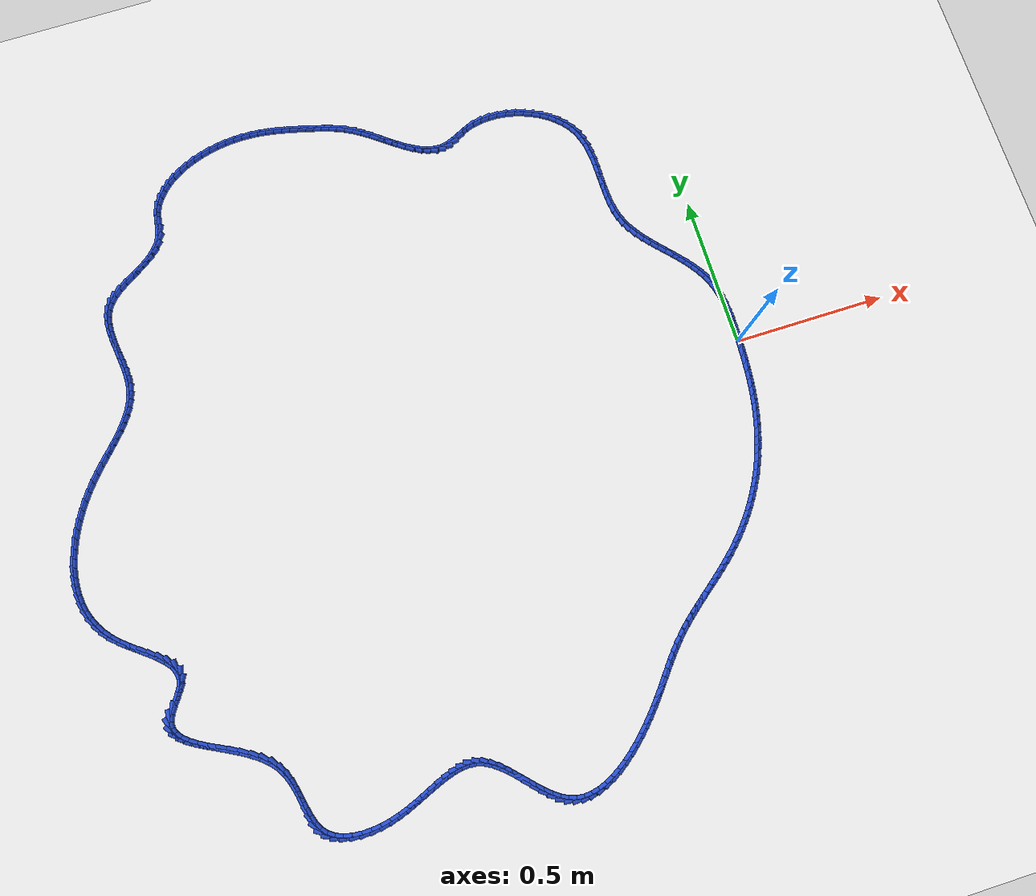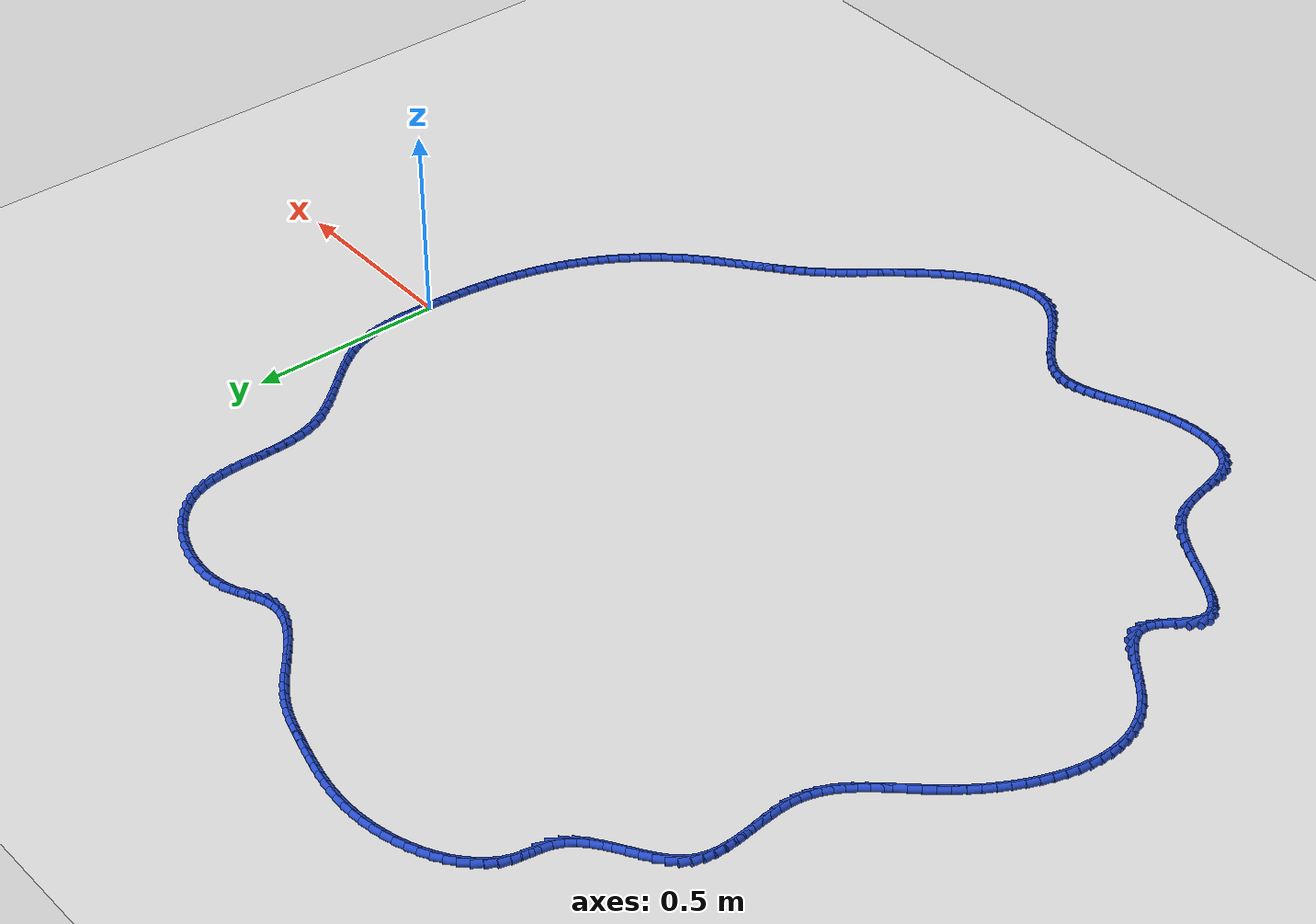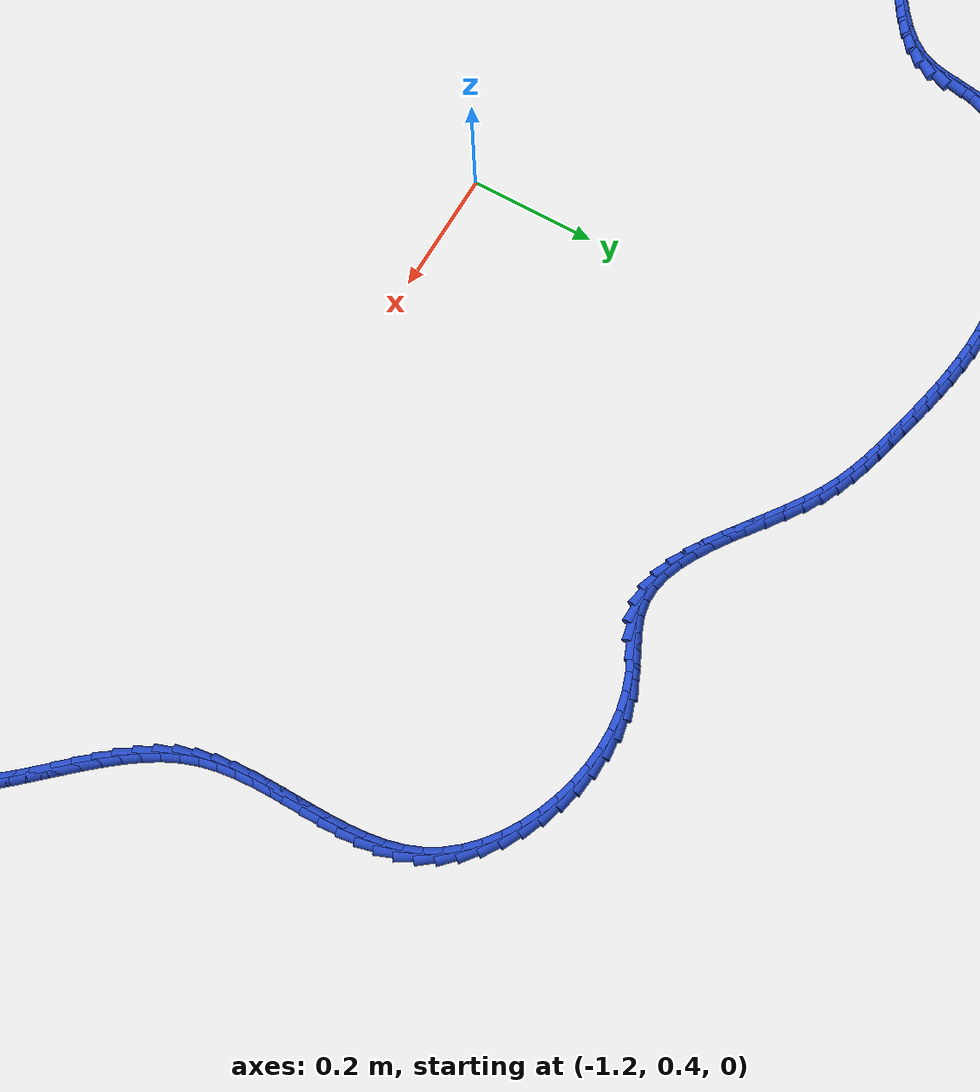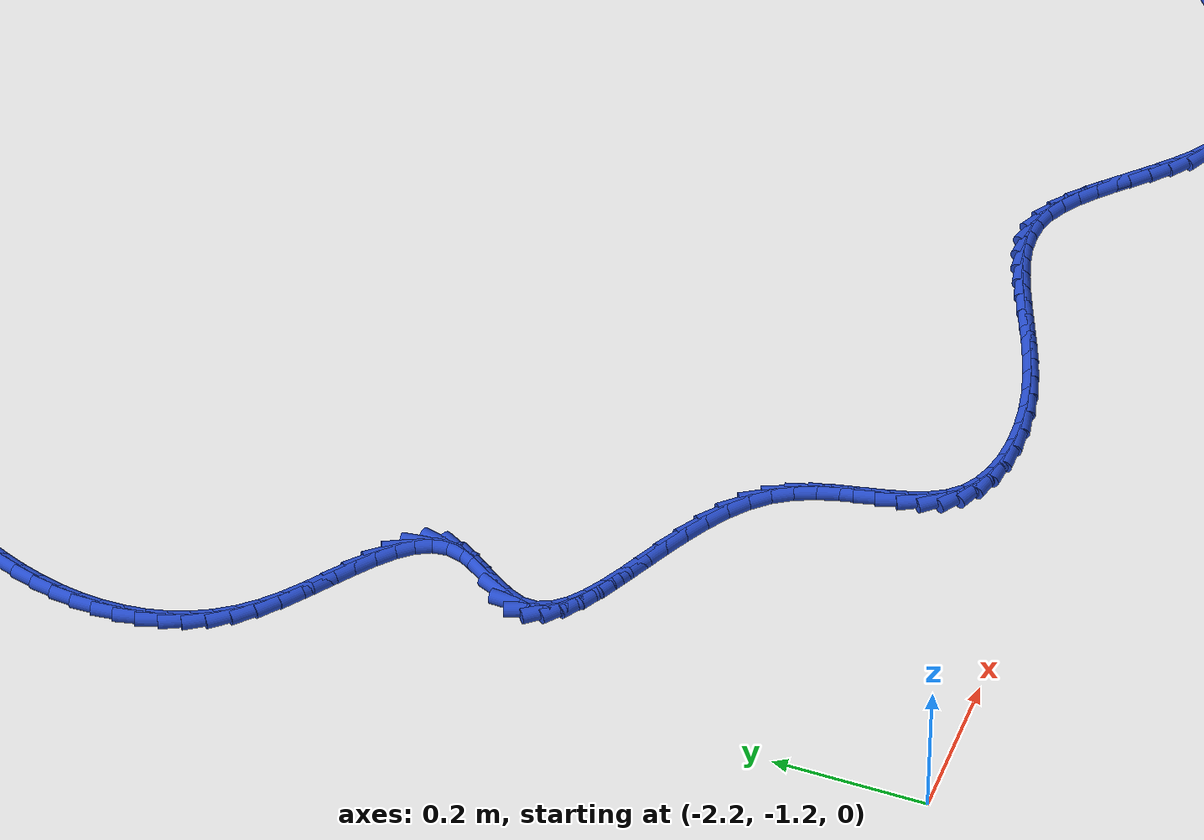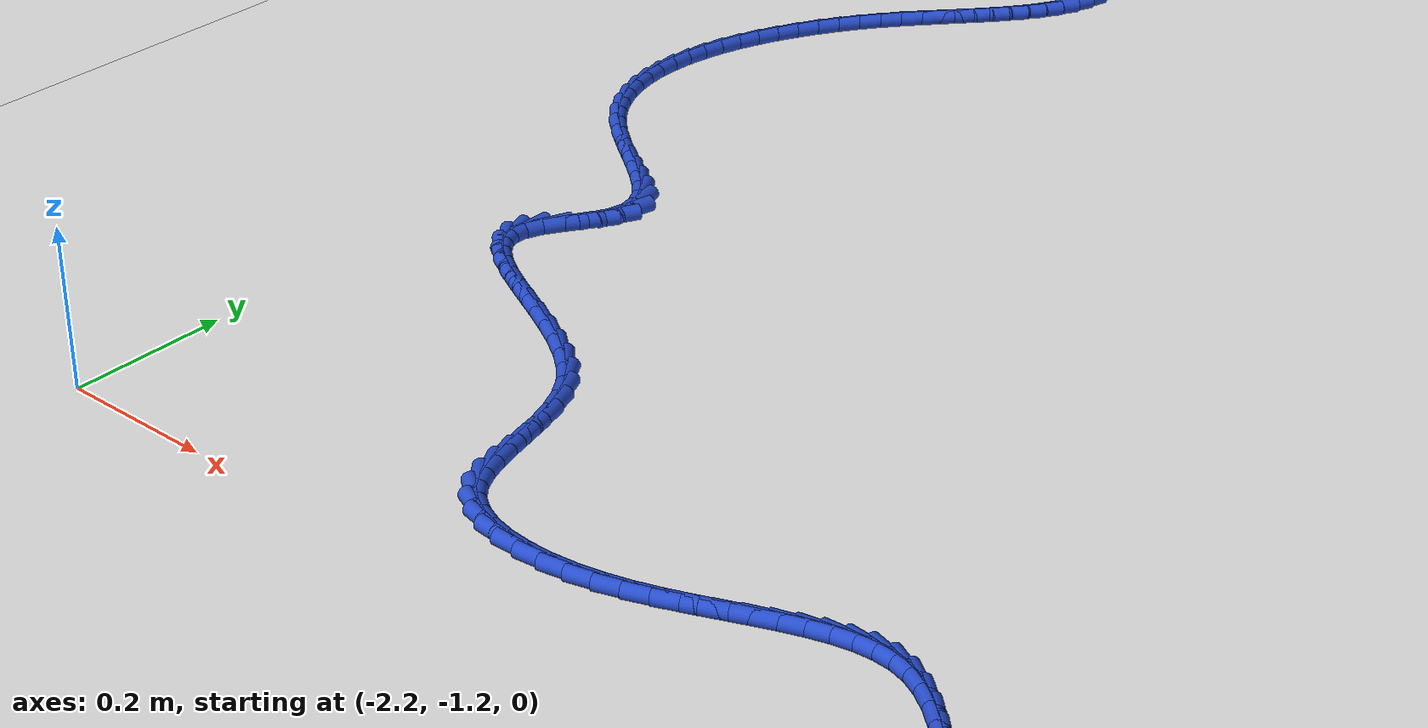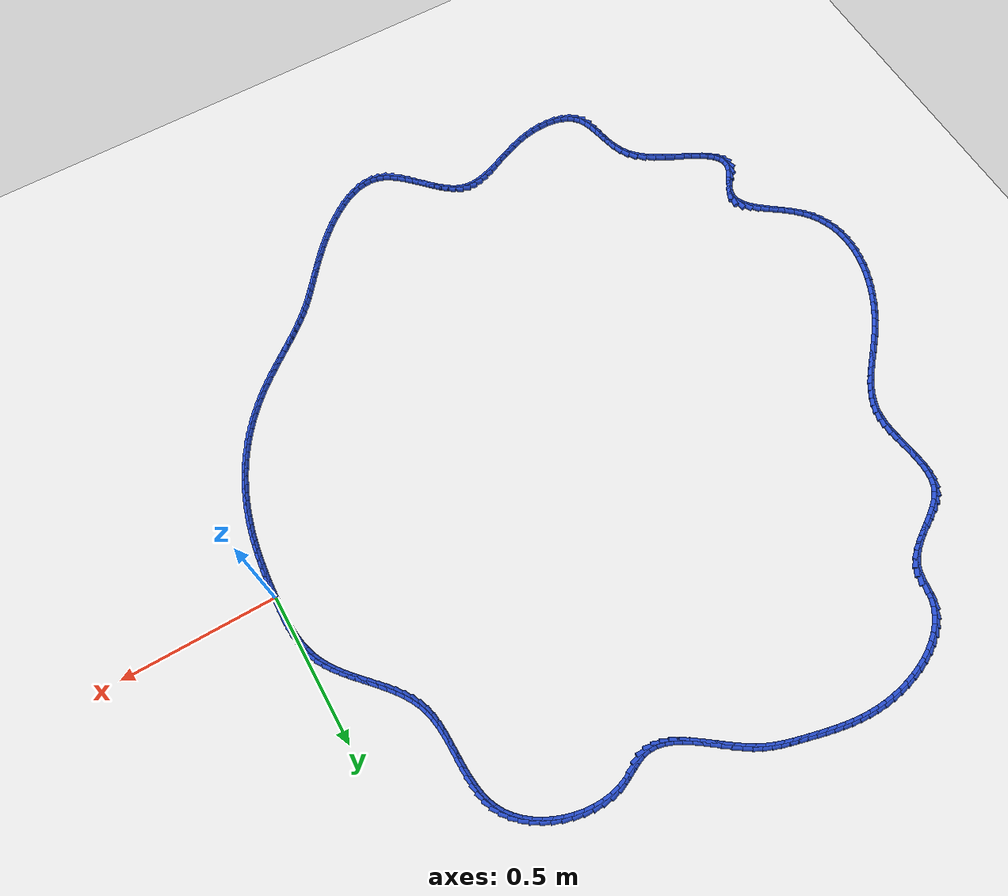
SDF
<sdf version="1.6">
 <world name="default">
  <light name="sun" type="directional">
   <pose>0 0 10 0 -0 0</pose>
   <diffuse>0.8 0.8 0.8 1</diffuse>
   <specular>0.2 0.2 0.2 1</specular>
   <attenuation>
    <range>1000</range>
    <constant>0.9</constant>
    <linear>0.01</linear>
    <quadratic>0.001</quadratic>
   </attenuation>
   <direction>-0.5 0.1 -0.9</direction>
  </light>
  <model name="ground_plane">
   <static>1</static>
   <link name="link">
    <collision name="collision">
     <geometry><plane><normal>0 0 1</normal><size>100 100</size></plane></geometry>
     <surface><friction><ode><mu>100</mu><mu2>50</mu2></ode></friction></surface>
    </collision>
    <visual name="visual">
     <cast_shadows>0</cast_shadows>
     <geometry><plane><normal>0 0 1</normal><size>100 100</size></plane></geometry>
     <material>
      <script><uri>file://media/materials/scripts/gazebo.material</uri><name>Gazebo/WhiteGlow</name></script>
     </material>
    </visual>
   </link>
  </model>
  <gravity>0 0 -9.8</gravity>
  <magnetic_field>6e-06 2.3e-05 -4.2e-05</magnetic_field>
  <atmosphere type="adiabatic"/>
  <physics name="default_physics" default="0" type="ode">
   <max_step_size>0.001</max_step_size>
   <real_time_factor>1</real_time_factor>
   <real_time_update_rate>1000</real_time_update_rate>
  </physics>
  <scene><ambient>0.4 0.4 0.4 1</ambient><background>0.7 0.7 0.7 1</background><shadows>1</shadows></scene>
  <spherical_coordinates>
   <surface_model>EARTH_WGS84</surface_model>
   <latitude_deg>0</latitude_deg>
   <longitude_deg>0</longitude_deg>
   <elevation>0</elevation>
   <heading_deg>0</heading_deg>
  </spherical_coordinates>
  <model name="line">
   <link name="link_0">
    <pose>-3.577867169202165e-18 3.469446951953614e-17 0.01 0 1.57 1.5313810276846365</pose>
    <collision name="collision">
     <geometry><cylinder><radius>0.01</radius><length>0.08</length></cylinder></geometry>
    </collision>
    <visual name="visual">
     <material>
      <script><name>Gazebo/Blue</name><uri>file://media/materials/scripts/gazebo.material</uri></script>
     </material>
     <geometry><cylinder><radius>0.01</radius><length>0.08</length></cylinder></geometry>
    </visual>
   </link>
   <link name="link_1">
    <pose>0.0011078297223571646 0.02809203513526441 0.01 0 1.57 1.5508251258644656</pose>
    <collision name="collision">
     <geometry><cylinder><radius>0.01</radius><length>0.08</length></cylinder></geometry>
    </collision>
    <visual name="visual">
     <material>
      <script><name>Gazebo/Blue</name><uri>file://media/materials/scripts/gazebo.material</uri></script>
     </material>
     <geometry><cylinder><radius>0.01</radius><length>0.08</length></cylinder></geometry>
    </visual>
   </link>
   <link name="link_2">
    <pose>0.0016709253579382133 0.056283668287402444 0.01 0 1.57 -1.5616062555757853</pose>
    <collision name="collision">
     <geometry><cylinder><radius>0.01</radius><length>0.08</length></cylinder></geometry>
    </collision>
    <visual name="visual">
     <material>
      <script><name>Gazebo/Blue</name><uri>file://media/materials/scripts/gazebo.material</uri></script>
     </material>
     <geometry><cylinder><radius>0.01</radius><length>0.08</length></cylinder></geometry>
    </visual>
   </link>
   <link name="link_3">
    <pose>0.001412394904609176 0.08441437248474258 0.01 0 1.57 -1.5222109770309682</pose>
    <collision name="collision">
     <geometry><cylinder><radius>0.01</radius><length>0.08</length></cylinder></geometry>
    </collision>
    <visual name="visual">
     <material>
      <script><name>Gazebo/Blue</name><uri>file://media/materials/scripts/gazebo.material</uri></script>
     </material>
     <geometry><cylinder><radius>0.01</radius><length>0.08</length></cylinder></geometry>
    </visual>
   </link>
   <link name="link_4">
    <pose>5.5346360236090044e-05 0.11232362075561338 0.01 0 1.57 -1.4718567219086012</pose>
    <collision name="collision">
     <geometry><cylinder><radius>0.01</radius><length>0.08</length></cylinder></geometry>
    </collision>
    <visual name="visual">
     <material>
      <script><name>Gazebo/Blue</name><uri>file://media/materials/scripts/gazebo.material</uri></script>
     </material>
     <geometry><cylinder><radius>0.01</radius><length>0.08</length></cylinder></geometry>
    </visual>
   </link>
   <link name="link_5">
    <pose>-0.0026771122773150057 0.1398508861283433 0.01 0 1.57 -1.4097138829830382</pose>
    <collision name="collision">
     <geometry><cylinder><radius>0.01</radius><length>0.08</length></cylinder></geometry>
    </collision>
    <visual name="visual">
     <material>
      <script><name>Gazebo/Blue</name><uri>file://media/materials/scripts/gazebo.material</uri></script>
     </material>
     <geometry><cylinder><radius>0.01</radius><length>0.08</length></cylinder></geometry>
    </visual>
   </link>
   <link name="link_6">
    <pose>-0.00706187301017808 0.16683564163126086 0.01 0 1.57 -1.33502317986975</pose>
    <collision name="collision">
     <geometry><cylinder><radius>0.01</radius><length>0.08</length></cylinder></geometry>
    </collision>
    <visual name="visual">
     <material>
      <script><name>Gazebo/Blue</name><uri>file://media/materials/scripts/gazebo.material</uri></script>
     </material>
     <geometry><cylinder><radius>0.01</radius><length>0.08</length></cylinder></geometry>
    </visual>
   </link>
   <link name="link_7">
    <pose>-0.013375827840487098 0.1931173602926946 0.01 0 1.57 -1.2473711202386364</pose>
    <collision name="collision">
     <geometry><cylinder><radius>0.01</radius><length>0.08</length></cylinder></geometry>
    </collision>
    <visual name="visual">
     <material>
      <script><name>Gazebo/Blue</name><uri>file://media/materials/scripts/gazebo.material</uri></script>
     </material>
     <geometry><cylinder><radius>0.01</radius><length>0.08</length></cylinder></geometry>
    </visual>
   </link>
   <link name="link_8">
    <pose>-0.02189586877037602 0.21853551514097308 0.01 0 1.57 -1.147712825434415</pose>
    <collision name="collision">
     <geometry><cylinder><radius>0.01</radius><length>0.08</length></cylinder></geometry>
    </collision>
    <visual name="visual">
     <material>
      <script><name>Gazebo/Blue</name><uri>file://media/materials/scripts/gazebo.material</uri></script>
     </material>
     <geometry><cylinder><radius>0.01</radius><length>0.08</length></cylinder></geometry>
    </visual>
   </link>
   <link name="link_9">
    <pose>-0.0328832979421568 0.24293705310615804 0.01 0 1.57 -1.0514697278287726</pose>
    <collision name="collision">
     <geometry><cylinder><radius>0.01</radius><length>0.08</length></cylinder></geometry>
    </collision>
    <visual name="visual">
     <material>
      <script><name>Gazebo/Blue</name><uri>file://media/materials/scripts/gazebo.material</uri></script>
     </material>
     <geometry><cylinder><radius>0.01</radius><length>0.08</length></cylinder></geometry>
    </visual>
   </link>
   <link name="link_10">
    <pose>-0.04625783000817345 0.26633268085461137 0.01 0 1.57 -0.9733686503471793</pose>
    <collision name="collision">
     <geometry><cylinder><radius>0.01</radius><length>0.08</length></cylinder></geometry>
    </collision>
    <visual name="visual">
     <material>
      <script><name>Gazebo/Blue</name><uri>file://media/materials/scripts/gazebo.material</uri></script>
     </material>
     <geometry><cylinder><radius>0.01</radius><length>0.08</length></cylinder></geometry>
    </visual>
   </link>
   <link name="link_11">
    <pose>-0.06160676697657685 0.28889246629558135 0.01 0 1.57 -0.9136602222577828</pose>
    <collision name="collision">
     <geometry><cylinder><radius>0.01</radius><length>0.08</length></cylinder></geometry>
    </collision>
    <visual name="visual">
     <material>
      <script><name>Gazebo/Blue</name><uri>file://media/materials/scripts/gazebo.material</uri></script>
     </material>
     <geometry><cylinder><radius>0.01</radius><length>0.08</length></cylinder></geometry>
    </visual>
   </link>
   <link name="link_12">
    <pose>-0.07850365639127553 0.3107930713369355 0.01 0 1.57 -0.8713924782951618</pose>
    <collision name="collision">
     <geometry><cylinder><radius>0.01</radius><length>0.08</length></cylinder></geometry>
    </collision>
    <visual name="visual">
     <material>
      <script><name>Gazebo/Blue</name><uri>file://media/materials/scripts/gazebo.material</uri></script>
     </material>
     <geometry><cylinder><radius>0.01</radius><length>0.08</length></cylinder></geometry>
    </visual>
   </link>
   <link name="link_13">
    <pose>-0.0965220457961781 0.3322111578865413 0.01 0 1.57 -0.8455578197980537</pose>
    <collision name="collision">
     <geometry><cylinder><radius>0.01</radius><length>0.08</length></cylinder></geometry>
    </collision>
    <visual name="visual">
     <material>
      <script><name>Gazebo/Blue</name><uri>file://media/materials/scripts/gazebo.material</uri></script>
     </material>
     <geometry><cylinder><radius>0.01</radius><length>0.08</length></cylinder></geometry>
    </visual>
   </link>
   <link name="link_14">
    <pose>-0.11523548273519316 0.3533233878522667 0.01 0 1.57 -0.8354251950677716</pose>
    <collision name="collision">
     <geometry><cylinder><radius>0.01</radius><length>0.08</length></cylinder></geometry>
    </collision>
    <visual name="visual">
     <material>
      <script><name>Gazebo/Blue</name><uri>file://media/materials/scripts/gazebo.material</uri></script>
     </material>
     <geometry><cylinder><radius>0.01</radius><length>0.08</length></cylinder></geometry>
    </visual>
   </link>
   <link name="link_15">
    <pose>-0.13421751475222926 0.3743064231419791 0.01 0 1.57 -0.8407010361707644</pose>
    <collision name="collision">
     <geometry><cylinder><radius>0.01</radius><length>0.08</length></cylinder></geometry>
    </collision>
    <visual name="visual">
     <material>
      <script><name>Gazebo/Blue</name><uri>file://media/materials/scripts/gazebo.material</uri></script>
     </material>
     <geometry><cylinder><radius>0.01</radius><length>0.08</length></cylinder></geometry>
    </visual>
   </link>
   <link name="link_16">
    <pose>-0.15304168939119492 0.3953369256635461 0.01 0 1.57 -0.86158426462308</pose>
    <collision name="collision">
     <geometry><cylinder><radius>0.01</radius><length>0.08</length></cylinder></geometry>
    </collision>
    <visual name="visual">
     <material>
      <script><name>Gazebo/Blue</name><uri>file://media/materials/scripts/gazebo.material</uri></script>
     </material>
     <geometry><cylinder><radius>0.01</radius><length>0.08</length></cylinder></geometry>
    </visual>
   </link>
   <link name="link_17">
    <pose>-0.17128155419599891 0.4165915573248355 0.01 0 1.57 -0.8987427125662087</pose>
    <collision name="collision">
     <geometry><cylinder><radius>0.01</radius><length>0.08</length></cylinder></geometry>
    </collision>
    <visual name="visual">
     <material>
      <script><name>Gazebo/Blue</name><uri>file://media/materials/scripts/gazebo.material</uri></script>
     </material>
     <geometry><cylinder><radius>0.01</radius><length>0.08</length></cylinder></geometry>
    </visual>
   </link>
   <link name="link_18">
    <pose>-0.18851065671054962 0.4382469800337148 0.01 0 1.57 -0.953194710009889</pose>
    <collision name="collision">
     <geometry><cylinder><radius>0.01</radius><length>0.08</length></cylinder></geometry>
    </collision>
    <visual name="visual">
     <material>
      <script><name>Gazebo/Blue</name><uri>file://media/materials/scripts/gazebo.material</uri></script>
     </material>
     <geometry><cylinder><radius>0.01</radius><length>0.08</length></cylinder></geometry>
    </visual>
   </link>
   <link name="link_19">
    <pose>-0.2043025444787557 0.4604798556980516 0.01 0 1.57 -1.02603705719187</pose>
    <collision name="collision">
     <geometry><cylinder><radius>0.01</radius><length>0.08</length></cylinder></geometry>
    </collision>
    <visual name="visual">
     <material>
      <script><name>Gazebo/Blue</name><uri>file://media/materials/scripts/gazebo.material</uri></script>
     </material>
     <geometry><cylinder><radius>0.01</radius><length>0.08</length></cylinder></geometry>
    </visual>
   </link>
   <link name="link_20">
    <pose>-0.21823076504452577 0.4834668462257137 0.01 0 1.57 -1.117935692472783</pose>
    <collision name="collision">
     <geometry><cylinder><radius>0.01</radius><length>0.08</length></cylinder></geometry>
    </collision>
    <visual name="visual">
     <material>
      <script><name>Gazebo/Blue</name><uri>file://media/materials/scripts/gazebo.material</uri></script>
     </material>
     <geometry><cylinder><radius>0.01</radius><length>0.08</length></cylinder></geometry>
    </visual>
   </link>
   <link name="link_21">
    <pose>-0.22986886595176842 0.5073846135245685 0.01 0 1.57 -1.227947509923445</pose>
    <collision name="collision">
     <geometry><cylinder><radius>0.01</radius><length>0.08</length></cylinder></geometry>
    </collision>
    <visual name="visual">
     <material>
      <script><name>Gazebo/Blue</name><uri>file://media/materials/scripts/gazebo.material</uri></script>
     </material>
     <geometry><cylinder><radius>0.01</radius><length>0.08</length></cylinder></geometry>
    </visual>
   </link>
   <link name="link_22">
    <pose>-0.2388000736481412 0.5324058281903175 0.01 0 1.57 -1.3380263961916572</pose>
    <collision name="collision">
     <geometry><cylinder><radius>0.01</radius><length>0.08</length></cylinder></geometry>
    </collision>
    <visual name="visual">
     <material>
      <script><name>Gazebo/Blue</name><uri>file://media/materials/scripts/gazebo.material</uri></script>
     </material>
     <geometry><cylinder><radius>0.01</radius><length>0.08</length></cylinder></geometry>
    </visual>
   </link>
   <link name="link_23">
    <pose>-0.24499630632778177 0.5585428750944877 0.01 0 1.57 -1.4259828190099542</pose>
    <collision name="collision">
     <geometry><cylinder><radius>0.01</radius><length>0.08</length></cylinder></geometry>
    </collision>
    <visual name="visual">
     <material>
      <script><name>Gazebo/Blue</name><uri>file://media/materials/scripts/gazebo.material</uri></script>
     </material>
     <geometry><cylinder><radius>0.01</radius><length>0.08</length></cylinder></geometry>
    </visual>
   </link>
   <link name="link_24">
    <pose>-0.24894171413925217 0.5855969088200715 0.01 0 1.57 -1.4912136509066753</pose>
    <collision name="collision">
     <geometry><cylinder><radius>0.01</radius><length>0.08</length></cylinder></geometry>
    </collision>
    <visual name="visual">
     <material>
      <script><name>Gazebo/Blue</name><uri>file://media/materials/scripts/gazebo.material</uri></script>
     </material>
     <geometry><cylinder><radius>0.01</radius><length>0.08</length></cylinder></geometry>
    </visual>
   </link>
   <link name="link_25">
    <pose>-0.25115542565638815 0.6133546598150582 0.01 0 1.57 -1.5353701760550509</pose>
    <collision name="collision">
     <geometry><cylinder><radius>0.01</radius><length>0.08</length></cylinder></geometry>
    </collision>
    <visual name="visual">
     <material>
      <script><name>Gazebo/Blue</name><uri>file://media/materials/scripts/gazebo.material</uri></script>
     </material>
     <geometry><cylinder><radius>0.01</radius><length>0.08</length></cylinder></geometry>
    </visual>
   </link>
   <link name="link_26">
    <pose>-0.2521565694530258 0.6416028585274374 0.01 0 1.57 -1.5600096957454845</pose>
    <collision name="collision">
     <geometry><cylinder><radius>0.01</radius><length>0.08</length></cylinder></geometry>
    </collision>
    <visual name="visual">
     <material>
      <script><name>Gazebo/Blue</name><uri>file://media/materials/scripts/gazebo.material</uri></script>
     </material>
     <geometry><cylinder><radius>0.01</radius><length>0.08</length></cylinder></geometry>
    </visual>
   </link>
   <link name="link_27">
    <pose>-0.25246427410300076 0.6701282354051993 0.01 0 1.57 -1.5661304840900139</pose>
    <collision name="collision">
     <geometry><cylinder><radius>0.01</radius><length>0.08</length></cylinder></geometry>
    </collision>
    <visual name="visual">
     <material>
      <script><name>Gazebo/Blue</name><uri>file://media/materials/scripts/gazebo.material</uri></script>
     </material>
     <geometry><cylinder><radius>0.01</radius><length>0.08</length></cylinder></geometry>
    </visual>
   </link>
   <link name="link_28">
    <pose>-0.25259766818014906 0.698717520896333 0.01 0 1.57 -1.5539830959671757</pose>
    <collision name="collision">
     <geometry><cylinder><radius>0.01</radius><length>0.08</length></cylinder></geometry>
    </collision>
    <visual name="visual">
     <material>
      <script><name>Gazebo/Blue</name><uri>file://media/materials/scripts/gazebo.material</uri></script>
     </material>
     <geometry><cylinder><radius>0.01</radius><length>0.08</length></cylinder></geometry>
    </visual>
   </link>
   <link name="link_29">
    <pose>-0.2530758802583066 0.7271574454488289 0.01 0 1.57 -1.5230304079722372</pose>
    <collision name="collision">
     <geometry><cylinder><radius>0.01</radius><length>0.08</length></cylinder></geometry>
    </collision>
    <visual name="visual">
     <material>
      <script><name>Gazebo/Blue</name><uri>file://media/materials/scripts/gazebo.material</uri></script>
     </material>
     <geometry><cylinder><radius>0.01</radius><length>0.08</length></cylinder></geometry>
    </visual>
   </link>
   <link name="link_30">
    <pose>-0.2544180389113091 0.7552347395106762 0.01 0 1.57 -1.4720244002931444</pose>
    <collision name="collision">
     <geometry><cylinder><radius>0.01</radius><length>0.08</length></cylinder></geometry>
    </collision>
    <visual name="visual">
     <material>
      <script><name>Gazebo/Blue</name><uri>file://media/materials/scripts/gazebo.material</uri></script>
     </material>
     <geometry><cylinder><radius>0.01</radius><length>0.08</length></cylinder></geometry>
    </visual>
   </link>
   <link name="link_31">
    <pose>-0.25714327271299253 0.7827361335298646 0.01 0 1.57 -1.399265712273153</pose>
    <collision name="collision">
     <geometry><cylinder><radius>0.01</radius><length>0.08</length></cylinder></geometry>
    </collision>
    <visual name="visual">
     <material>
      <script><name>Gazebo/Blue</name><uri>file://media/materials/scripts/gazebo.material</uri></script>
     </material>
     <geometry><cylinder><radius>0.01</radius><length>0.08</length></cylinder></geometry>
    </visual>
   </link>
   <link name="link_32">
    <pose>-0.2617707102371928 0.8094483579543844 0.01 0 1.57 -1.3032048906992089</pose>
    <collision name="collision">
     <geometry><cylinder><radius>0.01</radius><length>0.08</length></cylinder></geometry>
    </collision>
    <visual name="visual">
     <material>
      <script><name>Gazebo/Blue</name><uri>file://media/materials/scripts/gazebo.material</uri></script>
     </material>
     <geometry><cylinder><radius>0.01</radius><length>0.08</length></cylinder></geometry>
    </visual>
   </link>
   <link name="link_33">
    <pose>-0.2688194800577457 0.8351581432322245 0.01 0 1.57 -1.1835648277087818</pose>
    <collision name="collision">
     <geometry><cylinder><radius>0.01</radius><length>0.08</length></cylinder></geometry>
    </collision>
    <visual name="visual">
     <material>
      <script><name>Gazebo/Blue</name><uri>file://media/materials/scripts/gazebo.material</uri></script>
     </material>
     <geometry><cylinder><radius>0.01</radius><length>0.08</length></cylinder></geometry>
    </visual>
   </link>
   <link name="link_34">
    <pose>-0.27880871074848723 0.8596522198113755 0.01 0 1.57 -1.0438807030472712</pose>
    <collision name="collision">
     <geometry><cylinder><radius>0.01</radius><length>0.08</length></cylinder></geometry>
    </collision>
    <visual name="visual">
     <material>
      <script><name>Gazebo/Blue</name><uri>file://media/materials/scripts/gazebo.material</uri></script>
     </material>
     <geometry><cylinder><radius>0.01</radius><length>0.08</length></cylinder></geometry>
    </visual>
   </link>
   <link name="link_35">
    <pose>-0.2922287105430867 0.8827193092780393 0.01 0 1.57 -0.9048821901748001</pose>
    <collision name="collision">
     <geometry><cylinder><radius>0.01</radius><length>0.08</length></cylinder></geometry>
    </collision>
    <visual name="visual">
     <material>
      <script><name>Gazebo/Blue</name><uri>file://media/materials/scripts/gazebo.material</uri></script>
     </material>
     <geometry><cylinder><radius>0.01</radius><length>0.08</length></cylinder></geometry>
    </visual>
   </link>
   <link name="link_36">
    <pose>-0.3090897871484933 0.9041812954706969 0.01 0 1.57 -0.7800937554397911</pose>
    <collision name="collision">
     <geometry><cylinder><radius>0.01</radius><length>0.08</length></cylinder></geometry>
    </collision>
    <visual name="visual">
     <material>
      <script><name>Gazebo/Blue</name><uri>file://media/materials/scripts/gazebo.material</uri></script>
     </material>
     <geometry><cylinder><radius>0.01</radius><length>0.08</length></cylinder></geometry>
    </visual>
   </link>
   <link name="link_37">
    <pose>-0.32900609866637187 0.9238874313918554 0.01 0 1.57 -0.6677132965471272</pose>
    <collision name="collision">
     <geometry><cylinder><radius>0.01</radius><length>0.08</length></cylinder></geometry>
    </collision>
    <visual name="visual">
     <material>
      <script><name>Gazebo/Blue</name><uri>file://media/materials/scripts/gazebo.material</uri></script>
     </material>
     <geometry><cylinder><radius>0.01</radius><length>0.08</length></cylinder></geometry>
    </visual>
   </link>
   <link name="link_38">
    <pose>-0.3515799470677737 0.9416877891597792 0.01 0 1.57 -0.5650477634246551</pose>
    <collision name="collision">
     <geometry><cylinder><radius>0.01</radius><length>0.08</length></cylinder></geometry>
    </collision>
    <visual name="visual">
     <material>
      <script><name>Gazebo/Blue</name><uri>file://media/materials/scripts/gazebo.material</uri></script>
     </material>
     <geometry><cylinder><radius>0.01</radius><length>0.08</length></cylinder></geometry>
    </visual>
   </link>
   <link name="link_39">
    <pose>-0.3764136343237496 0.9574324408927315 0.01 0 1.57 -0.4693580459899538</pose>
    <collision name="collision">
     <geometry><cylinder><radius>0.01</radius><length>0.08</length></cylinder></geometry>
    </collision>
    <visual name="visual">
     <material>
      <script><name>Gazebo/Blue</name><uri>file://media/materials/scripts/gazebo.material</uri></script>
     </material>
     <geometry><cylinder><radius>0.01</radius><length>0.08</length></cylinder></geometry>
    </visual>
   </link>
   <link name="link_40">
    <pose>-0.40310946240535084 0.9709714587089772 0.01 0 1.57 -0.37803493548141825</pose>
    <collision name="collision">
     <geometry><cylinder><radius>0.01</radius><length>0.08</length></cylinder></geometry>
    </collision>
    <visual name="visual">
     <material>
      <script><name>Gazebo/Blue</name><uri>file://media/materials/scripts/gazebo.material</uri></script>
     </material>
     <geometry><cylinder><radius>0.01</radius><length>0.08</length></cylinder></geometry>
    </visual>
   </link>
   <link name="link_41">
    <pose>-0.4312697332836288 0.9821549147267801 0.01 0 1.57 -0.2886249701991375</pose>
    <collision name="collision">
     <geometry><cylinder><radius>0.01</radius><length>0.08</length></cylinder></geometry>
    </collision>
    <visual name="visual">
     <material>
      <script><name>Gazebo/Blue</name><uri>file://media/materials/scripts/gazebo.material</uri></script>
     </material>
     <geometry><cylinder><radius>0.01</radius><length>0.08</length></cylinder></geometry>
    </visual>
   </link>
   <link name="link_42">
    <pose>-0.46049674892963427 0.9908328810644043 0.01 0 1.57 -0.1987889834341735</pose>
    <collision name="collision">
     <geometry><cylinder><radius>0.01</radius><length>0.08</length></cylinder></geometry>
    </collision>
    <visual name="visual">
     <material>
      <script><name>Gazebo/Blue</name><uri>file://media/materials/scripts/gazebo.material</uri></script>
     </material>
     <geometry><cylinder><radius>0.01</radius><length>0.08</length></cylinder></geometry>
    </visual>
   </link>
   <link name="link_43">
    <pose>-0.4903928113144185 0.9968554298401135 0.01 0 1.57 -0.10624343257482734</pose>
    <collision name="collision">
     <geometry><cylinder><radius>0.01</radius><length>0.08</length></cylinder></geometry>
    </collision>
    <visual name="visual">
     <material>
      <script><name>Gazebo/Blue</name><uri>file://media/materials/scripts/gazebo.material</uri></script>
     </material>
     <geometry><cylinder><radius>0.01</radius><length>0.08</length></cylinder></geometry>
    </visual>
   </link>
   <link name="link_44">
    <pose>-0.5205602224090325 1.0000726331721723 0.01 0 1.57 -0.008718845273887716</pose>
    <collision name="collision">
     <geometry><cylinder><radius>0.01</radius><length>0.08</length></cylinder></geometry>
    </collision>
    <visual name="visual">
     <material>
      <script><name>Gazebo/Blue</name><uri>file://media/materials/scripts/gazebo.material</uri></script>
     </material>
     <geometry><cylinder><radius>0.01</radius><length>0.08</length></cylinder></geometry>
    </visual>
   </link>
   <link name="link_45">
    <pose>-0.5506012841845276 1.0003345631788445 0.01 0 1.57 0.09603023360826245</pose>
    <collision name="collision">
     <geometry><cylinder><radius>0.01</radius><length>0.08</length></cylinder></geometry>
    </collision>
    <visual name="visual">
     <material>
      <script><name>Gazebo/Blue</name><uri>file://media/materials/scripts/gazebo.material</uri></script>
     </material>
     <geometry><cylinder><radius>0.01</radius><length>0.08</length></cylinder></geometry>
    </visual>
   </link>
   <link name="link_46">
    <pose>-0.5801182986119544 0.9974912919783941 0.01 0 1.57 0.21011823832212112</pose>
    <collision name="collision">
     <geometry><cylinder><radius>0.01</radius><length>0.08</length></cylinder></geometry>
    </collision>
    <visual name="visual">
     <material>
      <script><name>Gazebo/Blue</name><uri>file://media/materials/scripts/gazebo.material</uri></script>
     </material>
     <geometry><cylinder><radius>0.01</radius><length>0.08</length></cylinder></geometry>
    </visual>
   </link>
   <link name="link_47">
    <pose>-0.6087135676623646 0.9913928916890855 0.01 0 1.57 0.33450263647705586</pose>
    <collision name="collision">
     <geometry><cylinder><radius>0.01</radius><length>0.08</length></cylinder></geometry>
    </collision>
    <visual name="visual">
     <material>
      <script><name>Gazebo/Blue</name><uri>file://media/materials/scripts/gazebo.material</uri></script>
     </material>
     <geometry><cylinder><radius>0.01</radius><length>0.08</length></cylinder></geometry>
    </visual>
   </link>
   <link name="link_48">
    <pose>-0.6359956990288026 0.9819106166274126 0.01 0 1.57 0.43161143432639726</pose>
    <collision name="collision">
     <geometry><cylinder><radius>0.01</radius><length>0.08</length></cylinder></geometry>
    </collision>
    <visual name="visual">
     <material>
      <script><name>Gazebo/Blue</name><uri>file://media/materials/scripts/gazebo.material</uri></script>
     </material>
     <geometry><cylinder><radius>0.01</radius><length>0.08</length></cylinder></geometry>
    </visual>
   </link>
   <link name="link_49">
    <pose>-0.6618912633317708 0.9699838230284478 0.01 0 1.57 0.4453379137519719</pose>
    <collision name="collision">
     <geometry><cylinder><radius>0.01</radius><length>0.08</length></cylinder></geometry>
    </collision>
    <visual name="visual">
     <material>
      <script><name>Gazebo/Blue</name><uri>file://media/materials/scripts/gazebo.material</uri></script>
     </material>
     <geometry><cylinder><radius>0.01</radius><length>0.08</length></cylinder></geometry>
    </visual>
   </link>
   <link name="link_50">
    <pose>-0.6867877747798431 0.9581002700643989 0.01 0 1.57 0.36275585915896386</pose>
    <collision name="collision">
     <geometry><cylinder><radius>0.01</radius><length>0.08</length></cylinder></geometry>
    </collision>
    <visual name="visual">
     <material>
      <script><name>Gazebo/Blue</name><uri>file://media/materials/scripts/gazebo.material</uri></script>
     </material>
     <geometry><cylinder><radius>0.01</radius><length>0.08</length></cylinder></geometry>
    </visual>
   </link>
   <link name="link_51">
    <pose>-0.7111088913319522 0.9488691310906029 0.01 0 1.57 0.17421064434219116</pose>
    <collision name="collision">
     <geometry><cylinder><radius>0.01</radius><length>0.08</length></cylinder></geometry>
    </collision>
    <visual name="visual">
     <material>
      <script><name>Gazebo/Blue</name><uri>file://media/materials/scripts/gazebo.material</uri></script>
     </material>
     <geometry><cylinder><radius>0.01</radius><length>0.08</length></cylinder></geometry>
    </visual>
   </link>
   <link name="link_52">
    <pose>-0.7352447755202031 0.9446213434269082 0.01 0 1.57 -0.041086386822635705</pose>
    <collision name="collision">
     <geometry><cylinder><radius>0.01</radius><length>0.08</length></cylinder></geometry>
    </collision>
    <visual name="visual">
     <material>
      <script><name>Gazebo/Blue</name><uri>file://media/materials/scripts/gazebo.material</uri></script>
     </material>
     <geometry><cylinder><radius>0.01</radius><length>0.08</length></cylinder></geometry>
    </visual>
   </link>
   <link name="link_53">
    <pose>-0.7593356543252002 0.9456117079303081 0.01 0 1.57 -0.22639034225342297</pose>
    <collision name="collision">
     <geometry><cylinder><radius>0.01</radius><length>0.08</length></cylinder></geometry>
    </collision>
    <visual name="visual">
     <material>
      <script><name>Gazebo/Blue</name><uri>file://media/materials/scripts/gazebo.material</uri></script>
     </material>
     <geometry><cylinder><radius>0.01</radius><length>0.08</length></cylinder></geometry>
    </visual>
   </link>
   <link name="link_54">
    <pose>-0.7834087933918054 0.9511566909686812 0.01 0 1.57 -0.37255685304346425</pose>
    <collision name="collision">
     <geometry><cylinder><radius>0.01</radius><length>0.08</length></cylinder></geometry>
    </collision>
    <visual name="visual">
     <material>
      <script><name>Gazebo/Blue</name><uri>file://media/materials/scripts/gazebo.material</uri></script>
     </material>
     <geometry><cylinder><radius>0.01</radius><length>0.08</length></cylinder></geometry>
    </visual>
   </link>
   <link name="link_55">
    <pose>-0.8074909050824676 0.9605681629659346 0.01 0 1.57 -0.4811034382538745</pose>
    <collision name="collision">
     <geometry><cylinder><radius>0.01</radius><length>0.08</length></cylinder></geometry>
    </collision>
    <visual name="visual">
     <material>
      <script><name>Gazebo/Blue</name><uri>file://media/materials/scripts/gazebo.material</uri></script>
     </material>
     <geometry><cylinder><radius>0.01</radius><length>0.08</length></cylinder></geometry>
    </visual>
   </link>
   <link name="link_56">
    <pose>-0.8316087017596355 0.973157994345975 0.01 0 1.57 -0.5576304165380404</pose>
    <collision name="collision">
     <geometry><cylinder><radius>0.01</radius><length>0.08</length></cylinder></geometry>
    </collision>
    <visual name="visual">
     <material>
      <script><name>Gazebo/Blue</name><uri>file://media/materials/scripts/gazebo.material</uri></script>
     </material>
     <geometry><cylinder><radius>0.01</radius><length>0.08</length></cylinder></geometry>
    </visual>
   </link>
   <link name="link_57">
    <pose>-0.8557888957857586 0.9882380555327096 0.01 0 1.57 -0.6077788800887954</pose>
    <collision name="collision">
     <geometry><cylinder><radius>0.01</radius><length>0.08</length></cylinder></geometry>
    </collision>
    <visual name="visual">
     <material>
      <script><name>Gazebo/Blue</name><uri>file://media/materials/scripts/gazebo.material</uri></script>
     </material>
     <geometry><cylinder><radius>0.01</radius><length>0.08</length></cylinder></geometry>
    </visual>
   </link>
   <link name="link_58">
    <pose>-0.8800581995232861 1.0051202169500453 0.01 0 1.57 -0.6357743593091727</pose>
    <collision name="collision">
     <geometry><cylinder><radius>0.01</radius><length>0.08</length></cylinder></geometry>
    </collision>
    <visual name="visual">
     <material>
      <script><name>Gazebo/Blue</name><uri>file://media/materials/scripts/gazebo.material</uri></script>
     </material>
     <geometry><cylinder><radius>0.01</radius><length>0.08</length></cylinder></geometry>
    </visual>
   </link>
   <link name="link_59">
    <pose>-0.9044433253346668 1.023116349021889 0.01 0 1.57 -0.64418512362138</pose>
    <collision name="collision">
     <geometry><cylinder><radius>0.01</radius><length>0.08</length></cylinder></geometry>
    </collision>
    <visual name="visual">
     <material>
      <script><name>Gazebo/Blue</name><uri>file://media/materials/scripts/gazebo.material</uri></script>
     </material>
     <geometry><cylinder><radius>0.01</radius><length>0.08</length></cylinder></geometry>
    </visual>
   </link>
   <link name="link_60">
    <pose>-0.9289709855823498 1.041538322172148 0.01 0 1.57 -0.6340278229280496</pose>
    <collision name="collision">
     <geometry><cylinder><radius>0.01</radius><length>0.08</length></cylinder></geometry>
    </collision>
    <visual name="visual">
     <material>
      <script><name>Gazebo/Blue</name><uri>file://media/materials/scripts/gazebo.material</uri></script>
     </material>
     <geometry><cylinder><radius>0.01</radius><length>0.08</length></cylinder></geometry>
    </visual>
   </link>
   <link name="link_61">
    <pose>-0.9536678926287843 1.0596980068247286 0.01 0 1.57 -0.6048856532522937</pose>
    <collision name="collision">
     <geometry><cylinder><radius>0.01</radius><length>0.08</length></cylinder></geometry>
    </collision>
    <visual name="visual">
     <material>
      <script><name>Gazebo/Blue</name><uri>file://media/materials/scripts/gazebo.material</uri></script>
     </material>
     <geometry><cylinder><radius>0.01</radius><length>0.08</length></cylinder></geometry>
    </visual>
   </link>
   <link name="link_62">
    <pose>-0.9785607588364191 1.0769072734035383 0.01 0 1.57 -0.5549694264853835</pose>
    <collision name="collision">
     <geometry><cylinder><radius>0.01</radius><length>0.08</length></cylinder></geometry>
    </collision>
    <visual name="visual">
     <material>
      <script><name>Gazebo/Blue</name><uri>file://media/materials/scripts/gazebo.material</uri></script>
     </material>
     <geometry><cylinder><radius>0.01</radius><length>0.08</length></cylinder></geometry>
    </visual>
   </link>
   <link name="link_63">
    <pose>-1.0036762965677035 1.0924779923324839 0.01 0 1.57 -0.4829893919452354</pose>
    <collision name="collision">
     <geometry><cylinder><radius>0.01</radius><length>0.08</length></cylinder></geometry>
    </collision>
    <visual name="visual">
     <material>
      <script><name>Gazebo/Blue</name><uri>file://media/materials/scripts/gazebo.material</uri></script>
     </material>
     <geometry><cylinder><radius>0.01</radius><length>0.08</length></cylinder></geometry>
    </visual>
   </link>
   <link name="link_64">
    <pose>-1.0290375413107897 1.1057778450481506 0.01 0 1.57 -0.40804307766473275</pose>
    <collision name="collision">
     <geometry><cylinder><radius>0.01</radius><length>0.08</length></cylinder></geometry>
    </collision>
    <visual name="visual">
     <material>
      <script><name>Gazebo/Blue</name><uri>file://media/materials/scripts/gazebo.material</uri></script>
     </material>
     <geometry><cylinder><radius>0.01</radius><length>0.08</length></cylinder></geometry>
    </visual>
   </link>
   <link name="link_65">
    <pose>-1.0546237559554095 1.1168389341361413 0.01 0 1.57 -0.34611922300045295</pose>
    <collision name="collision">
     <geometry><cylinder><radius>0.01</radius><length>0.08</length></cylinder></geometry>
    </collision>
    <visual name="visual">
     <material>
      <script><name>Gazebo/Blue</name><uri>file://media/materials/scripts/gazebo.material</uri></script>
     </material>
     <geometry><cylinder><radius>0.01</radius><length>0.08</length></cylinder></geometry>
    </visual>
   </link>
   <link name="link_66">
    <pose>-1.0803854666226946 1.1261295555428084 0.01 0 1.57 -0.29958416836178675</pose>
    <collision name="collision">
     <geometry><cylinder><radius>0.01</radius><length>0.08</length></cylinder></geometry>
    </collision>
    <visual name="visual">
     <material>
      <script><name>Gazebo/Blue</name><uri>file://media/materials/scripts/gazebo.material</uri></script>
     </material>
     <geometry><cylinder><radius>0.01</radius><length>0.08</length></cylinder></geometry>
    </visual>
   </link>
   <link name="link_67">
    <pose>-1.1062726976843331 1.1341256212334943 0.01 0 1.57 -0.2697142135009457</pose>
    <collision name="collision">
     <geometry><cylinder><radius>0.01</radius><length>0.08</length></cylinder></geometry>
    </collision>
    <visual name="visual">
     <material>
      <script><name>Gazebo/Blue</name><uri>file://media/materials/scripts/gazebo.material</uri></script>
     </material>
     <geometry><cylinder><radius>0.01</radius><length>0.08</length></cylinder></geometry>
    </visual>
   </link>
   <link name="link_68">
    <pose>-1.1322354735120148 1.141303043173542 0.01 0 1.57 -0.25687444221815975</pose>
    <collision name="collision">
     <geometry><cylinder><radius>0.01</radius><length>0.08</length></cylinder></geometry>
    </collision>
    <visual name="visual">
     <material>
      <script><name>Gazebo/Blue</name><uri>file://media/materials/scripts/gazebo.material</uri></script>
     </material>
     <geometry><cylinder><radius>0.01</radius><length>0.08</length></cylinder></geometry>
    </visual>
   </link>
   <link name="link_69">
    <pose>-1.158225278308185 1.148129981829618 0.01 0 1.57 -0.25075168695572775</pose>
    <collision name="collision">
     <geometry><cylinder><radius>0.01</radius><length>0.08</length></cylinder></geometry>
    </collision>
    <visual name="visual">
     <material>
      <script><name>Gazebo/Blue</name><uri>file://media/materials/scripts/gazebo.material</uri></script>
     </material>
     <geometry><cylinder><radius>0.01</radius><length>0.08</length></cylinder></geometry>
    </visual>
   </link>
   <link name="link_70">
    <pose>-1.1842462406682315 1.1547950632495674 0.01 0 1.57 -0.23813123399629751</pose>
    <collision name="collision">
     <geometry><cylinder><radius>0.01</radius><length>0.08</length></cylinder></geometry>
    </collision>
    <visual name="visual">
     <material>
      <script><name>Gazebo/Blue</name><uri>file://media/materials/scripts/gazebo.material</uri></script>
     </material>
     <geometry><cylinder><radius>0.01</radius><length>0.08</length></cylinder></geometry>
    </visual>
   </link>
   <link name="link_71">
    <pose>-1.21036859095569 1.1611359222681308 0.01 0 1.57 -0.21823260993447968</pose>
    <collision name="collision">
     <geometry><cylinder><radius>0.01</radius><length>0.08</length></cylinder></geometry>
    </collision>
    <visual name="visual">
     <material>
      <script><name>Gazebo/Blue</name><uri>file://media/materials/scripts/gazebo.material</uri></script>
     </material>
     <geometry><cylinder><radius>0.01</radius><length>0.08</length></cylinder></geometry>
    </visual>
   </link>
   <link name="link_72">
    <pose>-1.2366667546351762 1.1669679183156363 0.01 0 1.57 -0.19118780041252412</pose>
    <collision name="collision">
     <geometry><cylinder><radius>0.01</radius><length>0.08</length></cylinder></geometry>
    </collision>
    <visual name="visual">
     <material>
      <script><name>Gazebo/Blue</name><uri>file://media/materials/scripts/gazebo.material</uri></script>
     </material>
     <geometry><cylinder><radius>0.01</radius><length>0.08</length></cylinder></geometry>
    </visual>
   </link>
   <link name="link_73">
    <pose>-1.2632151571713068 1.172106410822413 0.01 0 1.57 -0.15722747520985952</pose>
    <collision name="collision">
     <geometry><cylinder><radius>0.01</radius><length>0.08</length></cylinder></geometry>
    </collision>
    <visual name="visual">
     <material>
      <script><name>Gazebo/Blue</name><uri>file://media/materials/scripts/gazebo.material</uri></script>
     </material>
     <geometry><cylinder><radius>0.01</radius><length>0.08</length></cylinder></geometry>
    </visual>
   </link>
   <link name="link_74">
    <pose>-1.2900882240286977 1.1763667592187899 0.01 0 1.57 -0.11671359246227216</pose>
    <collision name="collision">
     <geometry><cylinder><radius>0.01</radius><length>0.08</length></cylinder></geometry>
    </collision>
    <visual name="visual">
     <material>
      <script><name>Gazebo/Blue</name><uri>file://media/materials/scripts/gazebo.material</uri></script>
     </material>
     <geometry><cylinder><radius>0.01</radius><length>0.08</length></cylinder></geometry>
    </visual>
   </link>
   <link name="link_75">
    <pose>-1.317360380671966 1.1795643229350958 0.01 0 1.57 -0.07017082274021988</pose>
    <collision name="collision">
     <geometry><cylinder><radius>0.01</radius><length>0.08</length></cylinder></geometry>
    </collision>
    <visual name="visual">
     <material>
      <script><name>Gazebo/Blue</name><uri>file://media/materials/scripts/gazebo.material</uri></script>
     </material>
     <geometry><cylinder><radius>0.01</radius><length>0.08</length></cylinder></geometry>
    </visual>
   </link>
   <link name="link_76">
    <pose>-1.3451060525657281 1.1815144614016593 0.01 0 1.57 -0.018308540749948806</pose>
    <collision name="collision">
     <geometry><cylinder><radius>0.01</radius><length>0.08</length></cylinder></geometry>
    </collision>
    <visual name="visual">
     <material>
      <script><name>Gazebo/Blue</name><uri>file://media/materials/scripts/gazebo.material</uri></script>
     </material>
     <geometry><cylinder><radius>0.01</radius><length>0.08</length></cylinder></geometry>
    </visual>
   </link>
   <link name="link_77">
    <pose>-1.3733996651746003 1.1820325340488096 0.01 0 1.57 0.037975735328140414</pose>
    <collision name="collision">
     <geometry><cylinder><radius>0.01</radius><length>0.08</length></cylinder></geometry>
    </collision>
    <visual name="visual">
     <material>
      <script><name>Gazebo/Blue</name><uri>file://media/materials/scripts/gazebo.material</uri></script>
     </material>
     <geometry><cylinder><radius>0.01</radius><length>0.08</length></cylinder></geometry>
    </visual>
   </link>
   <link name="link_78">
    <pose>-1.4023156439631987 1.1809339003068748 0.01 0 1.57 0.09705486571900869</pose>
    <collision name="collision">
     <geometry><cylinder><radius>0.01</radius><length>0.08</length></cylinder></geometry>
    </collision>
    <visual name="visual">
     <material>
      <script><name>Gazebo/Blue</name><uri>file://media/materials/scripts/gazebo.material</uri></script>
     </material>
     <geometry><cylinder><radius>0.01</radius><length>0.08</length></cylinder></geometry>
    </visual>
   </link>
   <link name="link_79">
    <pose>-1.4318755244223627 1.1780559279037734 0.01 0 1.57 0.1557280858080401</pose>
    <collision name="collision">
     <geometry><cylinder><radius>0.01</radius><length>0.08</length></cylinder></geometry>
    </collision>
    <visual name="visual">
     <material>
      <script><name>Gazebo/Blue</name><uri>file://media/materials/scripts/gazebo.material</uri></script>
     </material>
     <geometry><cylinder><radius>0.01</radius><length>0.08</length></cylinder></geometry>
    </visual>
   </link>
   <link name="link_80">
    <pose>-1.4618129777390816 1.1733557691468417 0.01 0 1.57 0.2144910161183498</pose>
    <collision name="collision">
     <geometry><cylinder><radius>0.01</radius><length>0.08</length></cylinder></geometry>
    </collision>
    <visual name="visual">
     <material>
      <script><name>Gazebo/Blue</name><uri>file://media/materials/scripts/gazebo.material</uri></script>
     </material>
     <geometry><cylinder><radius>0.01</radius><length>0.08</length></cylinder></geometry>
    </visual>
   </link>
   <link name="link_81">
    <pose>-1.4917642134489448 1.1668311315729694 0.01 0 1.57 0.2749828854229942</pose>
    <collision name="collision">
     <geometry><cylinder><radius>0.01</radius><length>0.08</length></cylinder></geometry>
    </collision>
    <visual name="visual">
     <material>
      <script><name>Gazebo/Blue</name><uri>file://media/materials/scripts/gazebo.material</uri></script>
     </material>
     <geometry><cylinder><radius>0.01</radius><length>0.08</length></cylinder></geometry>
    </visual>
   </link>
   <link name="link_82">
    <pose>-1.5213653634581734 1.1584797550217674 0.01 0 1.57 0.338827552833776</pose>
    <collision name="collision">
     <geometry><cylinder><radius>0.01</radius><length>0.08</length></cylinder></geometry>
    </collision>
    <visual name="visual">
     <material>
      <script><name>Gazebo/Blue</name><uri>file://media/materials/scripts/gazebo.material</uri></script>
     </material>
     <geometry><cylinder><radius>0.01</radius><length>0.08</length></cylinder></geometry>
    </visual>
   </link>
   <link name="link_83">
    <pose>-1.5502525596729908 1.148299379332849 0.01 0 1.57 0.4077236835341433</pose>
    <collision name="collision">
     <geometry><cylinder><radius>0.01</radius><length>0.08</length></cylinder></geometry>
    </collision>
    <visual name="visual">
     <material>
      <script><name>Gazebo/Blue</name><uri>file://media/materials/scripts/gazebo.material</uri></script>
     </material>
     <geometry><cylinder><radius>0.01</radius><length>0.08</length></cylinder></geometry>
    </visual>
   </link>
   <link name="link_84">
    <pose>-1.5780619339996198 1.136287744345826 0.01 0 1.57 0.483510033436454</pose>
    <collision name="collision">
     <geometry><cylinder><radius>0.01</radius><length>0.08</length></cylinder></geometry>
    </collision>
    <visual name="visual">
     <material>
      <script><name>Gazebo/Blue</name><uri>file://media/materials/scripts/gazebo.material</uri></script>
     </material>
     <geometry><cylinder><radius>0.01</radius><length>0.08</length></cylinder></geometry>
    </visual>
   </link>
   <link name="link_85">
    <pose>-1.6044296183442839 1.1224425899003108 0.01 0 1.57 0.5681909639018403</pose>
    <collision name="collision">
     <geometry><cylinder><radius>0.01</radius><length>0.08</length></cylinder></geometry>
    </collision>
    <visual name="visual">
     <material>
      <script><name>Gazebo/Blue</name><uri>file://media/materials/scripts/gazebo.material</uri></script>
     </material>
     <geometry><cylinder><radius>0.01</radius><length>0.08</length></cylinder></geometry>
    </visual>
   </link>
   <link name="link_86">
    <pose>-1.6289917446132052 1.1067616558359148 0.01 0 1.57 0.6638869533108305</pose>
    <collision name="collision">
     <geometry><cylinder><radius>0.01</radius><length>0.08</length></cylinder></geometry>
    </collision>
    <visual name="visual">
     <material>
      <script><name>Gazebo/Blue</name><uri>file://media/materials/scripts/gazebo.material</uri></script>
     </material>
     <geometry><cylinder><radius>0.01</radius><length>0.08</length></cylinder></geometry>
    </visual>
   </link>
   <link name="link_87">
    <pose>-1.6513844447126071 1.0892426819922507 0.01 0 1.57 0.7726464606578581</pose>
    <collision name="collision">
     <geometry><cylinder><radius>0.01</radius><length>0.08</length></cylinder></geometry>
    </collision>
    <visual name="visual">
     <material>
      <script><name>Gazebo/Blue</name><uri>file://media/materials/scripts/gazebo.material</uri></script>
     </material>
     <geometry><cylinder><radius>0.01</radius><length>0.08</length></cylinder></geometry>
    </visual>
   </link>
   <link name="link_88">
    <pose>-1.6712438505487122 1.0698834082089304 0.01 0 1.57 0.8960330568182401</pose>
    <collision name="collision">
     <geometry><cylinder><radius>0.01</radius><length>0.08</length></cylinder></geometry>
    </collision>
    <visual name="visual">
     <material>
      <script><name>Gazebo/Blue</name><uri>file://media/materials/scripts/gazebo.material</uri></script>
     </material>
     <geometry><cylinder><radius>0.01</radius><length>0.08</length></cylinder></geometry>
    </visual>
   </link>
   <link name="link_89">
    <pose>-1.6882060940277437 1.048681574325566 0.01 0 1.57 1.034431491653979</pose>
    <collision name="collision">
     <geometry><cylinder><radius>0.01</radius><length>0.08</length></cylinder></geometry>
    </collision>
    <visual name="visual">
     <material>
      <script><name>Gazebo/Blue</name><uri>file://media/materials/scripts/gazebo.material</uri></script>
     </material>
     <geometry><cylinder><radius>0.01</radius><length>0.08</length></cylinder></geometry>
    </visual>
   </link>
   <link name="link_90">
    <pose>-1.701907307055924 1.0256349201817698 0.01 0 1.57 1.186181979838146</pose>
    <collision name="collision">
     <geometry><cylinder><radius>0.01</radius><length>0.08</length></cylinder></geometry>
    </collision>
    <visual name="visual">
     <material>
      <script><name>Gazebo/Blue</name><uri>file://media/materials/scripts/gazebo.material</uri></script>
     </material>
     <geometry><cylinder><radius>0.01</radius><length>0.08</length></cylinder></geometry>
    </visual>
   </link>
   <link name="link_91">
    <pose>-1.711983621539476 1.0007411856171538 0.01 0 1.57 1.3407738396615851</pose>
    <collision name="collision">
     <geometry><cylinder><radius>0.01</radius><length>0.08</length></cylinder></geometry>
    </collision>
    <visual name="visual">
     <material>
      <script><name>Gazebo/Blue</name><uri>file://media/materials/scripts/gazebo.material</uri></script>
     </material>
     <geometry><cylinder><radius>0.01</radius><length>0.08</length></cylinder></geometry>
    </visual>
   </link>
   <link name="link_92">
    <pose>-1.7182292993856116 0.9740692991099906 0.01 0 1.57 1.4129572980183338</pose>
    <collision name="collision">
     <geometry><cylinder><radius>0.01</radius><length>0.08</length></cylinder></geometry>
    </collision>
    <visual name="visual">
     <material>
      <script><name>Gazebo/Blue</name><uri>file://media/materials/scripts/gazebo.material</uri></script>
     </material>
     <geometry><cylinder><radius>0.01</radius><length>0.08</length></cylinder></geometry>
    </visual>
   </link>
   <link name="link_93">
    <pose>-1.7225922076990028 0.9466577219360093 0.01 0 1.57 1.3480170407148448</pose>
    <collision name="collision">
     <geometry><cylinder><radius>0.01</radius><length>0.08</length></cylinder></geometry>
    </collision>
    <visual name="visual">
     <material>
      <script><name>Gazebo/Blue</name><uri>file://media/materials/scripts/gazebo.material</uri></script>
     </material>
     <geometry><cylinder><radius>0.01</radius><length>0.08</length></cylinder></geometry>
    </visual>
   </link>
   <link name="link_94">
    <pose>-1.7285756925975946 0.920245177387812 0.01 0 1.57 1.1471956298870263</pose>
    <collision name="collision">
     <geometry><cylinder><radius>0.01</radius><length>0.08</length></cylinder></geometry>
    </collision>
    <visual name="visual">
     <material>
      <script><name>Gazebo/Blue</name><uri>file://media/materials/scripts/gazebo.material</uri></script>
     </material>
     <geometry><cylinder><radius>0.01</radius><length>0.08</length></cylinder></geometry>
    </visual>
   </link>
   <link name="link_95">
    <pose>-1.739330439019883 0.8963933541097926 0.01 0 1.57 0.9304805400473205</pose>
    <collision name="collision">
     <geometry><cylinder><radius>0.01</radius><length>0.08</length></cylinder></geometry>
    </collision>
    <visual name="visual">
     <material>
      <script><name>Gazebo/Blue</name><uri>file://media/materials/scripts/gazebo.material</uri></script>
     </material>
     <geometry><cylinder><radius>0.01</radius><length>0.08</length></cylinder></geometry>
    </visual>
   </link>
   <link name="link_96">
    <pose>-1.7551049724805214 0.8752204721219885 0.01 0 1.57 0.7674591538207465</pose>
    <collision name="collision">
     <geometry><cylinder><radius>0.01</radius><length>0.08</length></cylinder></geometry>
    </collision>
    <visual name="visual">
     <material>
      <script><name>Gazebo/Blue</name><uri>file://media/materials/scripts/gazebo.material</uri></script>
     </material>
     <geometry><cylinder><radius>0.01</radius><length>0.08</length></cylinder></geometry>
    </visual>
   </link>
   <link name="link_97">
    <pose>-1.7748309868601775 0.8561897890975716 0.01 0 1.57 0.6568580030948372</pose>
    <collision name="collision">
     <geometry><cylinder><radius>0.01</radius><length>0.08</length></cylinder></geometry>
    </collision>
    <visual name="visual">
     <material>
      <script><name>Gazebo/Blue</name><uri>file://media/materials/scripts/gazebo.material</uri></script>
     </material>
     <geometry><cylinder><radius>0.01</radius><length>0.08</length></cylinder></geometry>
    </visual>
   </link>
   <link name="link_98">
    <pose>-1.7974336121900345 0.8387612979990612 0.01 0 1.57 0.5907416033466514</pose>
    <collision name="collision">
     <geometry><cylinder><radius>0.01</radius><length>0.08</length></cylinder></geometry>
    </collision>
    <visual name="visual">
     <material>
      <script><name>Gazebo/Blue</name><uri>file://media/materials/scripts/gazebo.material</uri></script>
     </material>
     <geometry><cylinder><radius>0.01</radius><length>0.08</length></cylinder></geometry>
    </visual>
   </link>
   <link name="link_99">
    <pose>-1.8218379785012722 0.8223949917889752 0.01 0 1.57 0.5625128006963862</pose>
    <collision name="collision">
     <geometry><cylinder><radius>0.01</radius><length>0.08</length></cylinder></geometry>
    </collision>
    <visual name="visual">
     <material>
      <script><name>Gazebo/Blue</name><uri>file://media/materials/scripts/gazebo.material</uri></script>
     </material>
     <geometry><cylinder><radius>0.01</radius><length>0.08</length></cylinder></geometry>
    </visual>
   </link>
   <link name="link_100">
    <pose>-1.8469692158250728 0.8065508634298325 0.01 0 1.57 0.5693327987315252</pose>
    <collision name="collision">
     <geometry><cylinder><radius>0.01</radius><length>0.08</length></cylinder></geometry>
    </collision>
    <visual name="visual">
     <material>
      <script><name>Gazebo/Blue</name><uri>file://media/materials/scripts/gazebo.material</uri></script>
     </material>
     <geometry><cylinder><radius>0.01</radius><length>0.08</length></cylinder></geometry>
    </visual>
   </link>
   <link name="link_101">
    <pose>-1.8717524541926187 0.7906889058841522 0.01 0 1.57 0.6126636082556762</pose>
    <collision name="collision">
     <geometry><cylinder><radius>0.01</radius><length>0.08</length></cylinder></geometry>
    </collision>
    <visual name="visual">
     <material>
      <script><name>Gazebo/Blue</name><uri>file://media/materials/scripts/gazebo.material</uri></script>
     </material>
     <geometry><cylinder><radius>0.01</radius><length>0.08</length></cylinder></geometry>
    </visual>
   </link>
   <link name="link_102">
    <pose>-1.8951128236350907 0.7742691121144532 0.01 0 1.57 0.6984638401759388</pose>
    <collision name="collision">
     <geometry><cylinder><radius>0.01</radius><length>0.08</length></cylinder></geometry>
    </collision>
    <visual name="visual">
     <material>
      <script><name>Gazebo/Blue</name><uri>file://media/materials/scripts/gazebo.material</uri></script>
     </material>
     <geometry><cylinder><radius>0.01</radius><length>0.08</length></cylinder></geometry>
    </visual>
   </link>
   <link name="link_103">
    <pose>-1.9159754541836704 0.756751475083253 0.01 0 1.57 0.8365385955934447</pose>
    <collision name="collision">
     <geometry><cylinder><radius>0.01</radius><length>0.08</length></cylinder></geometry>
    </collision>
    <visual name="visual">
     <material>
      <script><name>Gazebo/Blue</name><uri>file://media/materials/scripts/gazebo.material</uri></script>
     </material>
     <geometry><cylinder><radius>0.01</radius><length>0.08</length></cylinder></geometry>
    </visual>
   </link>
   <link name="link_104">
    <pose>-1.9332654758695402 0.7375959877530713 0.01 0 1.57 1.0344301950333983</pose>
    <collision name="collision">
     <geometry><cylinder><radius>0.01</radius><length>0.08</length></cylinder></geometry>
    </collision>
    <visual name="visual">
     <material>
      <script><name>Gazebo/Blue</name><uri>file://media/materials/scripts/gazebo.material</uri></script>
     </material>
     <geometry><cylinder><radius>0.01</radius><length>0.08</length></cylinder></geometry>
    </visual>
   </link>
   <link name="link_105">
    <pose>-1.9459391984768044 0.7162777264544191 0.01 0 1.57 1.248348367734767</pose>
    <collision name="collision">
     <geometry><cylinder><radius>0.01</radius><length>0.08</length></cylinder></geometry>
    </collision>
    <visual name="visual">
     <material>
      <script><name>Gazebo/Blue</name><uri>file://media/materials/scripts/gazebo.material</uri></script>
     </material>
     <geometry><cylinder><radius>0.01</radius><length>0.08</length></cylinder></geometry>
    </visual>
   </link>
   <link name="link_106">
    <pose>-1.9538196985548604 0.6926910704583111 0.01 0 1.57 1.4201837935953527</pose>
    <collision name="collision">
     <geometry><cylinder><radius>0.01</radius><length>0.08</length></cylinder></geometry>
    </collision>
    <visual name="visual">
     <material>
      <script><name>Gazebo/Blue</name><uri>file://media/materials/scripts/gazebo.material</uri></script>
     </material>
     <geometry><cylinder><radius>0.01</radius><length>0.08</length></cylinder></geometry>
    </visual>
   </link>
   <link name="link_107">
    <pose>-1.9576891258969542 0.6671943557163901 0.01 0 1.57 1.5452618151788942</pose>
    <collision name="collision">
     <geometry><cylinder><radius>0.01</radius><length>0.08</length></cylinder></geometry>
    </collision>
    <visual name="visual">
     <material>
      <script><name>Gazebo/Blue</name><uri>file://media/materials/scripts/gazebo.material</uri></script>
     </material>
     <geometry><cylinder><radius>0.01</radius><length>0.08</length></cylinder></geometry>
    </visual>
   </link>
   <link name="link_108">
    <pose>-1.9583793306319626 0.640169960976709 0.01 0 1.57 -1.5120360182173296</pose>
    <collision name="collision">
     <geometry><cylinder><radius>0.01</radius><length>0.08</length></cylinder></geometry>
    </collision>
    <visual name="visual">
     <material>
      <script><name>Gazebo/Blue</name><uri>file://media/materials/scripts/gazebo.material</uri></script>
     </material>
     <geometry><cylinder><radius>0.01</radius><length>0.08</length></cylinder></geometry>
    </visual>
   </link>
   <link name="link_109">
    <pose>-1.956722162888762 0.6120002649873216 0.01 0 1.57 -1.4615748258199432</pose>
    <collision name="collision">
     <geometry><cylinder><radius>0.01</radius><length>0.08</length></cylinder></geometry>
    </collision>
    <visual name="visual">
     <material>
      <script><name>Gazebo/Blue</name><uri>file://media/materials/scripts/gazebo.material</uri></script>
     </material>
     <geometry><cylinder><radius>0.01</radius><length>0.08</length></cylinder></geometry>
    </visual>
   </link>
   <link name="link_110">
    <pose>-1.9535494727962284 0.5830676464962813 0.01 0 1.57 -1.4399901482570003</pose>
    <collision name="collision">
     <geometry><cylinder><radius>0.01</radius><length>0.08</length></cylinder></geometry>
    </collision>
    <visual name="visual">
     <material>
      <script><name>Gazebo/Blue</name><uri>file://media/materials/scripts/gazebo.material</uri></script>
     </material>
     <geometry><cylinder><radius>0.01</radius><length>0.08</length></cylinder></geometry>
    </visual>
   </link>
   <link name="link_111">
    <pose>-1.9496931104832382 0.5537544842516414 0.01 0 1.57 -1.4449545585034875</pose>
    <collision name="collision">
     <geometry><cylinder><radius>0.01</radius><length>0.08</length></cylinder></geometry>
    </collision>
    <visual name="visual">
     <material>
      <script><name>Gazebo/Blue</name><uri>file://media/materials/scripts/gazebo.material</uri></script>
     </material>
     <geometry><cylinder><radius>0.01</radius><length>0.08</length></cylinder></geometry>
    </visual>
   </link>
   <link name="link_112">
    <pose>-1.9459849260786686 0.5244431570014556 0.01 0 1.57 -1.4767630729621883</pose>
    <collision name="collision">
     <geometry><cylinder><radius>0.01</radius><length>0.08</length></cylinder></geometry>
    </collision>
    <visual name="visual">
     <material>
      <script><name>Gazebo/Blue</name><uri>file://media/materials/scripts/gazebo.material</uri></script>
     </material>
     <geometry><cylinder><radius>0.01</radius><length>0.08</length></cylinder></geometry>
    </visual>
   </link>
   <link name="link_113">
    <pose>-1.9432567697113954 0.49551604349377765 0.01 0 1.57 -1.5382701156890366</pose>
    <collision name="collision">
     <geometry><cylinder><radius>0.01</radius><length>0.08</length></cylinder></geometry>
    </collision>
    <visual name="visual">
     <material>
      <script><name>Gazebo/Blue</name><uri>file://media/materials/scripts/gazebo.material</uri></script>
     </material>
     <geometry><cylinder><radius>0.01</radius><length>0.08</length></cylinder></geometry>
    </visual>
   </link>
   <link name="link_114">
    <pose>-1.9423404915102949 0.46735552247666 0.01 0 1.57 1.506931182942452</pose>
    <collision name="collision">
     <geometry><cylinder><radius>0.01</radius><length>0.08</length></cylinder></geometry>
    </collision>
    <visual name="visual">
     <material>
      <script><name>Gazebo/Blue</name><uri>file://media/materials/scripts/gazebo.material</uri></script>
     </material>
     <geometry><cylinder><radius>0.01</radius><length>0.08</length></cylinder></geometry>
    </visual>
   </link>
   <link name="link_115">
    <pose>-1.9440679374086831 0.44034397055648034 0.01 0 1.57 1.3782835347966171</pose>
    <collision name="collision">
     <geometry><cylinder><radius>0.01</radius><length>0.08</length></cylinder></geometry>
    </collision>
    <visual name="visual">
     <material>
      <script><name>Gazebo/Blue</name><uri>file://media/materials/scripts/gazebo.material</uri></script>
     </material>
     <geometry><cylinder><radius>0.01</radius><length>0.08</length></cylinder></geometry>
    </visual>
   </link>
   <link name="link_116">
    <pose>-1.9490560926210962 0.41475408600384095 0.01 0 1.57 1.2499702489791575</pose>
    <collision name="collision">
     <geometry><cylinder><radius>0.01</radius><length>0.08</length></cylinder></geometry>
    </collision>
    <visual name="visual">
     <material>
      <script><name>Gazebo/Blue</name><uri>file://media/materials/scripts/gazebo.material</uri></script>
     </material>
     <geometry><cylinder><radius>0.01</radius><length>0.08</length></cylinder></geometry>
    </visual>
   </link>
   <link name="link_117">
    <pose>-1.9571309104806736 0.3904547749918891 0.01 0 1.57 1.1354602323575012</pose>
    <collision name="collision">
     <geometry><cylinder><radius>0.01</radius><length>0.08</length></cylinder></geometry>
    </collision>
    <visual name="visual">
     <material>
      <script><name>Gazebo/Blue</name><uri>file://media/materials/scripts/gazebo.material</uri></script>
     </material>
     <geometry><cylinder><radius>0.01</radius><length>0.08</length></cylinder></geometry>
    </visual>
   </link>
   <link name="link_118">
    <pose>-1.967936347660481 0.36722204122697044 0.01 0 1.57 1.0387625685012478</pose>
    <collision name="collision">
     <geometry><cylinder><radius>0.01</radius><length>0.08</length></cylinder></geometry>
    </collision>
    <visual name="visual">
     <material>
      <script><name>Gazebo/Blue</name><uri>file://media/materials/scripts/gazebo.material</uri></script>
     </material>
     <geometry><cylinder><radius>0.01</radius><length>0.08</length></cylinder></geometry>
    </visual>
   </link>
   <link name="link_119">
    <pose>-1.9811163608335847 0.344831888415431 0.01 0 1.57 0.9613524092617884</pose>
    <collision name="collision">
     <geometry><cylinder><radius>0.01</radius><length>0.08</length></cylinder></geometry>
    </collision>
    <visual name="visual">
     <material>
      <script><name>Gazebo/Blue</name><uri>file://media/materials/scripts/gazebo.material</uri></script>
     </material>
     <geometry><cylinder><radius>0.01</radius><length>0.08</length></cylinder></geometry>
    </visual>
   </link>
   <link name="link_120">
    <pose>-1.9963149066730503 0.32306032026361653 0.01 0 1.57 0.9029545458814607</pose>
    <collision name="collision">
     <geometry><cylinder><radius>0.01</radius><length>0.08</length></cylinder></geometry>
    </collision>
    <visual name="visual">
     <material>
      <script><name>Gazebo/Blue</name><uri>file://media/materials/scripts/gazebo.material</uri></script>
     </material>
     <geometry><cylinder><radius>0.01</radius><length>0.08</length></cylinder></geometry>
    </visual>
   </link>
   <link name="link_121">
    <pose>-2.0131759418519453 0.30168334047787293 0.01 0 1.57 0.8624262521462508</pose>
    <collision name="collision">
     <geometry><cylinder><radius>0.01</radius><length>0.08</length></cylinder></geometry>
    </collision>
    <visual name="visual">
     <material>
      <script><name>Gazebo/Blue</name><uri>file://media/materials/scripts/gazebo.material</uri></script>
     </material>
     <geometry><cylinder><radius>0.01</radius><length>0.08</length></cylinder></geometry>
    </visual>
   </link>
   <link name="link_122">
    <pose>-2.031343423043335 0.28047695276454615 0.01 0 1.57 0.8383953286288205</pose>
    <collision name="collision">
     <geometry><cylinder><radius>0.01</radius><length>0.08</length></cylinder></geometry>
    </collision>
    <visual name="visual">
     <material>
      <script><name>Gazebo/Blue</name><uri>file://media/materials/scripts/gazebo.material</uri></script>
     </material>
     <geometry><cylinder><radius>0.01</radius><length>0.08</length></cylinder></geometry>
    </visual>
   </link>
   <link name="link_123">
    <pose>-2.050461306920287 0.2592171608299823 0.01 0 1.57 0.8296111301917639</pose>
    <collision name="collision">
     <geometry><cylinder><radius>0.01</radius><length>0.08</length></cylinder></geometry>
    </collision>
    <visual name="visual">
     <material>
      <script><name>Gazebo/Blue</name><uri>file://media/materials/scripts/gazebo.material</uri></script>
     </material>
     <geometry><cylinder><radius>0.01</radius><length>0.08</length></cylinder></geometry>
    </visual>
   </link>
   <link name="link_124">
    <pose>-2.0701735501558662 0.23767996838052657 0.01 0 1.57 0.8350850820106905</pose>
    <collision name="collision">
     <geometry><cylinder><radius>0.01</radius><length>0.08</length></cylinder></geometry>
    </collision>
    <visual name="visual">
     <material>
      <script><name>Gazebo/Blue</name><uri>file://media/materials/scripts/gazebo.material</uri></script>
     </material>
     <geometry><cylinder><radius>0.01</radius><length>0.08</length></cylinder></geometry>
    </visual>
   </link>
   <link name="link_125">
    <pose>-2.09012410942314 0.21564137912252526 0.01 0 1.57 0.8541013558745589</pose>
    <collision name="collision">
     <geometry><cylinder><radius>0.01</radius><length>0.08</length></cylinder></geometry>
    </collision>
    <visual name="visual">
     <material>
      <script><name>Gazebo/Blue</name><uri>file://media/materials/scripts/gazebo.material</uri></script>
     </material>
     <geometry><cylinder><radius>0.01</radius><length>0.08</length></cylinder></geometry>
    </visual>
   </link>
   <link name="link_126">
    <pose>-2.1099569413951746 0.19287739676232418 0.01 0 1.57 0.8861485407205125</pose>
    <collision name="collision">
     <geometry><cylinder><radius>0.01</radius><length>0.08</length></cylinder></geometry>
    </collision>
    <visual name="visual">
     <material>
      <script><name>Gazebo/Blue</name><uri>file://media/materials/scripts/gazebo.material</uri></script>
     </material>
     <geometry><cylinder><radius>0.01</radius><length>0.08</length></cylinder></geometry>
    </visual>
   </link>
   <link name="link_127">
    <pose>-2.129316004044674 0.16916402735309155 0.01 0 1.57 0.9285538691560973</pose>
    <collision name="collision">
     <geometry><cylinder><radius>0.01</radius><length>0.08</length></cylinder></geometry>
    </collision>
    <visual name="visual">
     <material>
      <script><name>Gazebo/Blue</name><uri>file://media/materials/scripts/gazebo.material</uri></script>
     </material>
     <geometry><cylinder><radius>0.01</radius><length>0.08</length></cylinder></geometry>
    </visual>
   </link>
   <link name="link_128">
    <pose>-2.147882228121463 0.14434404054359912 0.01 0 1.57 0.9732227315222464</pose>
    <collision name="collision">
     <geometry><cylinder><radius>0.01</radius><length>0.08</length></cylinder></geometry>
    </collision>
    <visual name="visual">
     <material>
      <script><name>Gazebo/Blue</name><uri>file://media/materials/scripts/gazebo.material</uri></script>
     </material>
     <geometry><cylinder><radius>0.01</radius><length>0.08</length></cylinder></geometry>
    </visual>
   </link>
   <link name="link_129">
    <pose>-2.1654701657499036 0.11850149279169164 0.01 0 1.57 1.0189442171665566</pose>
    <collision name="collision">
     <geometry><cylinder><radius>0.01</radius><length>0.08</length></cylinder></geometry>
    </collision>
    <visual name="visual">
     <material>
      <script><name>Gazebo/Blue</name><uri>file://media/materials/scripts/gazebo.material</uri></script>
     </material>
     <geometry><cylinder><radius>0.01</radius><length>0.08</length></cylinder></geometry>
    </visual>
   </link>
   <link name="link_130">
    <pose>-2.181924545205012 0.09177493114197098 0.01 0 1.57 1.066391288916727</pose>
    <collision name="collision">
     <geometry><cylinder><radius>0.01</radius><length>0.08</length></cylinder></geometry>
    </collision>
    <visual name="visual">
     <material>
      <script><name>Gazebo/Blue</name><uri>file://media/materials/scripts/gazebo.material</uri></script>
     </material>
     <geometry><cylinder><radius>0.01</radius><length>0.08</length></cylinder></geometry>
    </visual>
   </link>
   <link name="link_131">
    <pose>-2.1970900947618075 0.06430290263903905 0.01 0 1.57 1.1162506188491033</pose>
    <collision name="collision">
     <geometry><cylinder><radius>0.01</radius><length>0.08</length></cylinder></geometry>
    </collision>
    <visual name="visual">
     <material>
      <script><name>Gazebo/Blue</name><uri>file://media/materials/scripts/gazebo.material</uri></script>
     </material>
     <geometry><cylinder><radius>0.01</radius><length>0.08</length></cylinder></geometry>
    </visual>
   </link>
   <link name="link_132">
    <pose>-2.210811542695306 0.036223954327497636 0.01 0 1.57 1.1692383535626314</pose>
    <collision name="collision">
     <geometry><cylinder><radius>0.01</radius><length>0.08</length></cylinder></geometry>
    </collision>
    <visual name="visual">
     <material>
      <script><name>Gazebo/Blue</name><uri>file://media/materials/scripts/gazebo.material</uri></script>
     </material>
     <geometry><cylinder><radius>0.01</radius><length>0.08</length></cylinder></geometry>
    </visual>
   </link>
   <link name="link_133">
    <pose>-2.222933617280527 0.007676633251948568 0.01 0 1.57 1.2261099222320515</pose>
    <collision name="collision">
     <geometry><cylinder><radius>0.01</radius><length>0.08</length></cylinder></geometry>
    </collision>
    <visual name="visual">
     <material>
      <script><name>Gazebo/Blue</name><uri>file://media/materials/scripts/gazebo.material</uri></script>
     </material>
     <geometry><cylinder><radius>0.01</radius><length>0.08</length></cylinder></geometry>
    </visual>
   </link>
   <link name="link_134">
    <pose>-2.2333010467924863 -0.021200513543005825 0.01 0 1.57 1.2876611017947563</pose>
    <collision name="collision">
     <geometry><cylinder><radius>0.01</radius><length>0.08</length></cylinder></geometry>
    </collision>
    <visual name="visual">
     <material>
      <script><name>Gazebo/Blue</name><uri>file://media/materials/scripts/gazebo.material</uri></script>
     </material>
     <geometry><cylinder><radius>0.01</radius><length>0.08</length></cylinder></geometry>
    </visual>
   </link>
   <link name="link_135">
    <pose>-2.241758559506203 -0.05026893901276465 0.01 0 1.57 1.3547154472637721</pose>
    <collision name="collision">
     <geometry><cylinder><radius>0.01</radius><length>0.08</length></cylinder></geometry>
    </collision>
    <visual name="visual">
     <material>
      <script><name>Gazebo/Blue</name><uri>file://media/materials/scripts/gazebo.material</uri></script>
     </material>
     <geometry><cylinder><radius>0.01</radius><length>0.08</length></cylinder></geometry>
    </visual>
   </link>
   <link name="link_136">
    <pose>-2.2481508836966944 -0.07939009611272597 0.01 0 1.57 1.4280907364871451</pose>
    <collision name="collision">
     <geometry><cylinder><radius>0.01</radius><length>0.08</length></cylinder></geometry>
    </collision>
    <visual name="visual">
     <material>
      <script><name>Gazebo/Blue</name><uri>file://media/materials/scripts/gazebo.material</uri></script>
     </material>
     <geometry><cylinder><radius>0.01</radius><length>0.08</length></cylinder></geometry>
    </visual>
   </link>
   <link name="link_137">
    <pose>-2.2523227476389778 -0.10842543779828677 0.01 0 1.57 1.5085349760921503</pose>
    <collision name="collision">
     <geometry><cylinder><radius>0.01</radius><length>0.08</length></cylinder></geometry>
    </collision>
    <visual name="visual">
     <material>
      <script><name>Gazebo/Blue</name><uri>file://media/materials/scripts/gazebo.material</uri></script>
     </material>
     <geometry><cylinder><radius>0.01</radius><length>0.08</length></cylinder></geometry>
    </visual>
   </link>
   <link name="link_138">
    <pose>-2.25411887960807 -0.13723641702484676 0.01 0 1.57 -1.5449700284535788</pose>
    <collision name="collision">
     <geometry><cylinder><radius>0.01</radius><length>0.08</length></cylinder></geometry>
    </collision>
    <visual name="visual">
     <material>
      <script><name>Gazebo/Blue</name><uri>file://media/materials/scripts/gazebo.material</uri></script>
     </material>
     <geometry><cylinder><radius>0.01</radius><length>0.08</length></cylinder></geometry>
    </visual>
   </link>
   <link name="link_139">
    <pose>-2.2533840078789904 -0.1656844867478025 0.01 0 1.57 -1.448985164145226</pose>
    <collision name="collision">
     <geometry><cylinder><radius>0.01</radius><length>0.08</length></cylinder></geometry>
    </collision>
    <visual name="visual">
     <material>
      <script><name>Gazebo/Blue</name><uri>file://media/materials/scripts/gazebo.material</uri></script>
     </material>
     <geometry><cylinder><radius>0.01</radius><length>0.08</length></cylinder></geometry>
    </visual>
   </link>
   <link name="link_140">
    <pose>-2.2499628607267557 -0.19363109992255306 0.01 0 1.57 -1.3453480342210302</pose>
    <collision name="collision">
     <geometry><cylinder><radius>0.01</radius><length>0.08</length></cylinder></geometry>
    </collision>
    <visual name="visual">
     <material>
      <script><name>Gazebo/Blue</name><uri>file://media/materials/scripts/gazebo.material</uri></script>
     </material>
     <geometry><cylinder><radius>0.01</radius><length>0.08</length></cylinder></geometry>
    </visual>
   </link>
   <link name="link_141">
    <pose>-2.2437001664263834 -0.22093770950449726 0.01 0 1.57 -1.2349716382738567</pose>
    <collision name="collision">
     <geometry><cylinder><radius>0.01</radius><length>0.08</length></cylinder></geometry>
    </collision>
    <visual name="visual">
     <material>
      <script><name>Gazebo/Blue</name><uri>file://media/materials/scripts/gazebo.material</uri></script>
     </material>
     <geometry><cylinder><radius>0.01</radius><length>0.08</length></cylinder></geometry>
    </visual>
   </link>
   <link name="link_142">
    <pose>-2.234440653252891 -0.2474657684490317 0.01 0 1.57 -1.119527624433542</pose>
    <collision name="collision">
     <geometry><cylinder><radius>0.01</radius><length>0.08</length></cylinder></geometry>
    </collision>
    <visual name="visual">
     <material>
      <script><name>Gazebo/Blue</name><uri>file://media/materials/scripts/gazebo.material</uri></script>
     </material>
     <geometry><cylinder><radius>0.01</radius><length>0.08</length></cylinder></geometry>
    </visual>
   </link>
   <link name="link_143">
    <pose>-2.2220290494812964 -0.2730767297115561 0.01 0 1.57 -1.0013801900100083</pose>
    <collision name="collision">
     <geometry><cylinder><radius>0.01</radius><length>0.08</length></cylinder></geometry>
    </collision>
    <visual name="visual">
     <material>
      <script><name>Gazebo/Blue</name><uri>file://media/materials/scripts/gazebo.material</uri></script>
     </material>
     <geometry><cylinder><radius>0.01</radius><length>0.08</length></cylinder></geometry>
    </visual>
   </link>
   <link name="link_144">
    <pose>-2.206310083386618 -0.29763204624746714 0.01 0 1.57 -0.883326903998448</pose>
    <collision name="collision">
     <geometry><cylinder><radius>0.01</radius><length>0.08</length></cylinder></geometry>
    </collision>
    <visual name="visual">
     <material>
      <script><name>Gazebo/Blue</name><uri>file://media/materials/scripts/gazebo.material</uri></script>
     </material>
     <geometry><cylinder><radius>0.01</radius><length>0.08</length></cylinder></geometry>
    </visual>
   </link>
   <link name="link_145">
    <pose>-2.187128483243872 -0.3209931710121645 0.01 0 1.57 -0.7724691279451963</pose>
    <collision name="collision">
     <geometry><cylinder><radius>0.01</radius><length>0.08</length></cylinder></geometry>
    </collision>
    <visual name="visual">
     <material>
      <script><name>Gazebo/Blue</name><uri>file://media/materials/scripts/gazebo.material</uri></script>
     </material>
     <geometry><cylinder><radius>0.01</radius><length>0.08</length></cylinder></geometry>
    </visual>
   </link>
   <link name="link_146">
    <pose>-2.164479134887181 -0.3430642945828293 0.01 0 1.57 -0.6955905774156843</pose>
    <collision name="collision">
     <geometry><cylinder><radius>0.01</radius><length>0.08</length></cylinder></geometry>
    </collision>
    <visual name="visual">
     <material>
      <script><name>Gazebo/Blue</name><uri>file://media/materials/scripts/gazebo.material</uri></script>
     </material>
     <geometry><cylinder><radius>0.01</radius><length>0.08</length></cylinder></geometry>
    </visual>
   </link>
   <link name="link_147">
    <pose>-2.1393583095922493 -0.36403462037594714 0.01 0 1.57 -0.6564622899365692</pose>
    <collision name="collision">
     <geometry><cylinder><radius>0.01</radius><length>0.08</length></cylinder></geometry>
    </collision>
    <visual name="visual">
     <material>
      <script><name>Gazebo/Blue</name><uri>file://media/materials/scripts/gazebo.material</uri></script>
     </material>
     <geometry><cylinder><radius>0.01</radius><length>0.08</length></cylinder></geometry>
    </visual>
   </link>
   <link name="link_148">
    <pose>-2.1131719465932868 -0.38420995089480225 0.01 0 1.57 -0.6509606968045747</pose>
    <collision name="collision">
     <geometry><cylinder><radius>0.01</radius><length>0.08</length></cylinder></geometry>
    </collision>
    <visual name="visual">
     <material>
      <script><name>Gazebo/Blue</name><uri>file://media/materials/scripts/gazebo.material</uri></script>
     </material>
     <geometry><cylinder><radius>0.01</radius><length>0.08</length></cylinder></geometry>
    </visual>
   </link>
   <link name="link_149">
    <pose>-2.0873272124886473 -0.4038964379732437 0.01 0 1.57 -0.6804600346426491</pose>
    <collision name="collision">
     <geometry><cylinder><radius>0.01</radius><length>0.08</length></cylinder></geometry>
    </collision>
    <visual name="visual">
     <material>
      <script><name>Gazebo/Blue</name><uri>file://media/materials/scripts/gazebo.material</uri></script>
     </material>
     <geometry><cylinder><radius>0.01</radius><length>0.08</length></cylinder></geometry>
    </visual>
   </link>
   <link name="link_150">
    <pose>-2.0632312738766867 -0.42340023344511846 0.01 0 1.57 -0.7530503090300141</pose>
    <collision name="collision">
     <geometry><cylinder><radius>0.01</radius><length>0.08</length></cylinder></geometry>
    </collision>
    <visual name="visual">
     <material>
      <script><name>Gazebo/Blue</name><uri>file://media/materials/scripts/gazebo.material</uri></script>
     </material>
     <geometry><cylinder><radius>0.01</radius><length>0.08</length></cylinder></geometry>
    </visual>
   </link>
   <link name="link_151">
    <pose>-2.0422912973557588 -0.44302748914427514 0.01 0 1.57 -0.8860626486881282</pose>
    <collision name="collision">
     <geometry><cylinder><radius>0.01</radius><length>0.08</length></cylinder></geometry>
    </collision>
    <visual name="visual">
     <material>
      <script><name>Gazebo/Blue</name><uri>file://media/materials/scripts/gazebo.material</uri></script>
     </material>
     <geometry><cylinder><radius>0.01</radius><length>0.08</length></cylinder></geometry>
    </visual>
   </link>
   <link name="link_152">
    <pose>-2.025914449524218 -0.4630843569045626 0.01 0 1.57 -1.106754935985622</pose>
    <collision name="collision">
     <geometry><cylinder><radius>0.01</radius><length>0.08</length></cylinder></geometry>
    </collision>
    <visual name="visual">
     <material>
      <script><name>Gazebo/Blue</name><uri>file://media/materials/scripts/gazebo.material</uri></script>
     </material>
     <geometry><cylinder><radius>0.01</radius><length>0.08</length></cylinder></geometry>
    </visual>
   </link>
   <link name="link_153">
    <pose>-2.01550789698042 -0.48387698855982764 0.01 0 1.57 -1.4329469118991998</pose>
    <collision name="collision">
     <geometry><cylinder><radius>0.01</radius><length>0.08</length></cylinder></geometry>
    </collision>
    <visual name="visual">
     <material>
      <script><name>Gazebo/Blue</name><uri>file://media/materials/scripts/gazebo.material</uri></script>
     </material>
     <geometry><cylinder><radius>0.01</radius><length>0.08</length></cylinder></geometry>
    </visual>
   </link>
   <link name="link_154">
    <pose>-2.012478806322719 -0.5057115359439195 0.01 0 1.57 1.3303568811636042</pose>
    <collision name="collision">
     <geometry><cylinder><radius>0.01</radius><length>0.08</length></cylinder></geometry>
    </collision>
    <visual name="visual">
     <material>
      <script><name>Gazebo/Blue</name><uri>file://media/materials/scripts/gazebo.material</uri></script>
     </material>
     <geometry><cylinder><radius>0.01</radius><length>0.08</length></cylinder></geometry>
    </visual>
   </link>
   <link name="link_155">
    <pose>-2.0181589845004253 -0.5288786780725527 0.01 0 1.57 1.073680397625172</pose>
    <collision name="collision">
     <geometry><cylinder><radius>0.01</radius><length>0.08</length></cylinder></geometry>
    </collision>
    <visual name="visual">
     <material>
      <script><name>Gazebo/Blue</name><uri>file://media/materials/scripts/gazebo.material</uri></script>
     </material>
     <geometry><cylinder><radius>0.01</radius><length>0.08</length></cylinder></geometry>
    </visual>
   </link>
   <link name="link_156">
    <pose>-2.0313246734668295 -0.5531443862045715 0.01 0 1.57 0.9832884168162731</pose>
    <collision name="collision">
     <geometry><cylinder><radius>0.01</radius><length>0.08</length></cylinder></geometry>
    </collision>
    <visual name="visual">
     <material>
      <script><name>Gazebo/Blue</name><uri>file://media/materials/scripts/gazebo.material</uri></script>
     </material>
     <geometry><cylinder><radius>0.01</radius><length>0.08</length></cylinder></geometry>
    </visual>
   </link>
   <link name="link_157">
    <pose>-2.0476338490776773 -0.5776343902385217 0.01 0 1.57 1.0108201186510835</pose>
    <collision name="collision">
     <geometry><cylinder><radius>0.01</radius><length>0.08</length></cylinder></geometry>
    </collision>
    <visual name="visual">
     <material>
      <script><name>Gazebo/Blue</name><uri>file://media/materials/scripts/gazebo.material</uri></script>
     </material>
     <geometry><cylinder><radius>0.01</radius><length>0.08</length></cylinder></geometry>
    </visual>
   </link>
   <link name="link_158">
    <pose>-2.0625551883462605 -0.6014355532974411 0.01 0 1.57 1.1845032348227698</pose>
    <collision name="collision">
     <geometry><cylinder><radius>0.01</radius><length>0.08</length></cylinder></geometry>
    </collision>
    <visual name="visual">
     <material>
      <script><name>Gazebo/Blue</name><uri>file://media/materials/scripts/gazebo.material</uri></script>
     </material>
     <geometry><cylinder><radius>0.01</radius><length>0.08</length></cylinder></geometry>
    </visual>
   </link>
   <link name="link_159">
    <pose>-2.071586961240989 -0.6236414688173467 0.01 0 1.57 1.5384990069696682</pose>
    <collision name="collision">
     <geometry><cylinder><radius>0.01</radius><length>0.08</length></cylinder></geometry>
    </collision>
    <visual name="visual">
     <material>
      <script><name>Gazebo/Blue</name><uri>file://media/materials/scripts/gazebo.material</uri></script>
     </material>
     <geometry><cylinder><radius>0.01</radius><length>0.08</length></cylinder></geometry>
    </visual>
   </link>
   <link name="link_160">
    <pose>-2.0722383534936157 -0.6438030719364153 0.01 0 1.57 -1.2093703985232973</pose>
    <collision name="collision">
     <geometry><cylinder><radius>0.01</radius><length>0.08</length></cylinder></geometry>
    </collision>
    <visual name="visual">
     <material>
      <script><name>Gazebo/Blue</name><uri>file://media/materials/scripts/gazebo.material</uri></script>
     </material>
     <geometry><cylinder><radius>0.01</radius><length>0.08</length></cylinder></geometry>
    </visual>
   </link>
   <link name="link_161">
    <pose>-2.065278894460966 -0.6622127963330889 0.01 0 1.57 -0.9000656160312671</pose>
    <collision name="collision">
     <geometry><cylinder><radius>0.01</radius><length>0.08</length></cylinder></geometry>
    </collision>
    <visual name="visual">
     <material>
      <script><name>Gazebo/Blue</name><uri>file://media/materials/scripts/gazebo.material</uri></script>
     </material>
     <geometry><cylinder><radius>0.01</radius><length>0.08</length></cylinder></geometry>
    </visual>
   </link>
   <link name="link_162">
    <pose>-2.051776032961039 -0.679230831379985 0.01 0 1.57 -0.700027727535812</pose>
    <collision name="collision">
     <geometry><cylinder><radius>0.01</radius><length>0.08</length></cylinder></geometry>
    </collision>
    <visual name="visual">
     <material>
      <script><name>Gazebo/Blue</name><uri>file://media/materials/scripts/gazebo.material</uri></script>
     </material>
     <geometry><cylinder><radius>0.01</radius><length>0.08</length></cylinder></geometry>
    </visual>
   </link>
   <link name="link_163">
    <pose>-2.0327972178118356 -0.6952173664497245 0.01 0 1.57 -0.5797782949481165</pose>
    <collision name="collision">
     <geometry><cylinder><radius>0.01</radius><length>0.08</length></cylinder></geometry>
    </collision>
    <visual name="visual">
     <material>
      <script><name>Gazebo/Blue</name><uri>file://media/materials/scripts/gazebo.material</uri></script>
     </material>
     <geometry><cylinder><radius>0.01</radius><length>0.08</length></cylinder></geometry>
    </visual>
   </link>
   <link name="link_164">
    <pose>-2.009409897831356 -0.710532590914926 0.01 0 1.57 -0.5115191209317548</pose>
    <collision name="collision">
     <geometry><cylinder><radius>0.01</radius><length>0.08</length></cylinder></geometry>
    </collision>
    <visual name="visual">
     <material>
      <script><name>Gazebo/Blue</name><uri>file://media/materials/scripts/gazebo.material</uri></script>
     </material>
     <geometry><cylinder><radius>0.01</radius><length>0.08</length></cylinder></geometry>
    </visual>
   </link>
   <link name="link_165">
    <pose>-1.982681521837598 -0.7255366941482096 0.01 0 1.57 -0.4787628391784567</pose>
    <collision name="collision">
     <geometry><cylinder><radius>0.01</radius><length>0.08</length></cylinder></geometry>
    </collision>
    <visual name="visual">
     <material>
      <script><name>Gazebo/Blue</name><uri>file://media/materials/scripts/gazebo.material</uri></script>
     </material>
     <geometry><cylinder><radius>0.01</radius><length>0.08</length></cylinder></geometry>
    </visual>
   </link>
   <link name="link_166">
    <pose>-1.9536795386485635 -0.7405898655221939 0.01 0 1.57 -0.47309287863700056</pose>
    <collision name="collision">
     <geometry><cylinder><radius>0.01</radius><length>0.08</length></cylinder></geometry>
    </collision>
    <visual name="visual">
     <material>
      <script><name>Gazebo/Blue</name><uri>file://media/materials/scripts/gazebo.material</uri></script>
     </material>
     <geometry><cylinder><radius>0.01</radius><length>0.08</length></cylinder></geometry>
    </visual>
   </link>
   <link name="link_167">
    <pose>-1.9234713970822508 -0.7560522944094993 0.01 0 1.57 -0.4911594763447392</pose>
    <collision name="collision">
     <geometry><cylinder><radius>0.01</radius><length>0.08</length></cylinder></geometry>
    </collision>
    <visual name="visual">
     <material>
      <script><name>Gazebo/Blue</name><uri>file://media/materials/scripts/gazebo.material</uri></script>
     </material>
     <geometry><cylinder><radius>0.01</radius><length>0.08</length></cylinder></geometry>
    </visual>
   </link>
   <link name="link_168">
    <pose>-1.893124545956661 -0.7722841701827439 0.01 0 1.57 -0.533155790951373</pose>
    <collision name="collision">
     <geometry><cylinder><radius>0.01</radius><length>0.08</length></cylinder></geometry>
    </collision>
    <visual name="visual">
     <material>
      <script><name>Gazebo/Blue</name><uri>file://media/materials/scripts/gazebo.material</uri></script>
     </material>
     <geometry><cylinder><radius>0.01</radius><length>0.08</length></cylinder></geometry>
    </visual>
   </link>
   <link name="link_169">
    <pose>-1.8637064340897922 -0.7896456822145481 0.01 0 1.57 -0.6022567647852997</pose>
    <collision name="collision">
     <geometry><cylinder><radius>0.01</radius><length>0.08</length></cylinder></geometry>
    </collision>
    <visual name="visual">
     <material>
      <script><name>Gazebo/Blue</name><uri>file://media/materials/scripts/gazebo.material</uri></script>
     </material>
     <geometry><cylinder><radius>0.01</radius><length>0.08</length></cylinder></geometry>
    </visual>
   </link>
   <link name="link_170">
    <pose>-1.8362845102996463 -0.8084970198775309 0.01 0 1.57 -0.7044180009083288</pose>
    <collision name="collision">
     <geometry><cylinder><radius>0.01</radius><length>0.08</length></cylinder></geometry>
    </collision>
    <visual name="visual">
     <material>
      <script><name>Gazebo/Blue</name><uri>file://media/materials/scripts/gazebo.material</uri></script>
     </material>
     <geometry><cylinder><radius>0.01</radius><length>0.08</length></cylinder></geometry>
    </visual>
   </link>
   <link name="link_171">
    <pose>-1.811926223404222 -0.8291983725443115 0.01 0 1.57 -0.8475441155079375</pose>
    <collision name="collision">
     <geometry><cylinder><radius>0.01</radius><length>0.08</length></cylinder></geometry>
    </collision>
    <visual name="visual">
     <material>
      <script><name>Gazebo/Blue</name><uri>file://media/materials/scripts/gazebo.material</uri></script>
     </material>
     <geometry><cylinder><radius>0.01</radius><length>0.08</length></cylinder></geometry>
    </visual>
   </link>
   <link name="link_172">
    <pose>-1.7916990222215183 -0.8521099295875105 0.01 0 1.57 -1.0252533397626606</pose>
    <collision name="collision">
     <geometry><cylinder><radius>0.01</radius><length>0.08</length></cylinder></geometry>
    </collision>
    <visual name="visual">
     <material>
      <script><name>Gazebo/Blue</name><uri>file://media/materials/scripts/gazebo.material</uri></script>
     </material>
     <geometry><cylinder><radius>0.01</radius><length>0.08</length></cylinder></geometry>
    </visual>
   </link>
   <link name="link_173">
    <pose>-1.7763356216051185 -0.8774207477852843 0.01 0 1.57 -1.177505290112843</pose>
    <collision name="collision">
     <geometry><cylinder><radius>0.01</radius><length>0.08</length></cylinder></geometry>
    </collision>
    <visual name="visual">
     <material>
      <script><name>Gazebo/Blue</name><uri>file://media/materials/scripts/gazebo.material</uri></script>
     </material>
     <geometry><cylinder><radius>0.01</radius><length>0.08</length></cylinder></geometry>
    </visual>
   </link>
   <link name="link_174">
    <pose>-1.7650765846749181 -0.9045570219876362 0.01 0 1.57 -1.283345946575304</pose>
    <collision name="collision">
     <geometry><cylinder><radius>0.01</radius><length>0.08</length></cylinder></geometry>
    </collision>
    <visual name="visual">
     <material>
      <script><name>Gazebo/Blue</name><uri>file://media/materials/scripts/gazebo.material</uri></script>
     </material>
     <geometry><cylinder><radius>0.01</radius><length>0.08</length></cylinder></geometry>
    </visual>
   </link>
   <link name="link_175">
    <pose>-1.7567468485774853 -0.9327324584455531 0.01 0 1.57 -1.343491907849067</pose>
    <collision name="collision">
     <geometry><cylinder><radius>0.01</radius><length>0.08</length></cylinder></geometry>
    </collision>
    <visual name="visual">
     <material>
      <script><name>Gazebo/Blue</name><uri>file://media/materials/scripts/gazebo.material</uri></script>
     </material>
     <geometry><cylinder><radius>0.01</radius><length>0.08</length></cylinder></geometry>
    </visual>
   </link>
   <link name="link_176">
    <pose>-1.7501713328941089 -0.9611607544297845 0.01 0 1.57 -1.3590550371621462</pose>
    <collision name="collision">
     <geometry><cylinder><radius>0.01</radius><length>0.08</length></cylinder></geometry>
    </collision>
    <visual name="visual">
     <material>
      <script><name>Gazebo/Blue</name><uri>file://media/materials/scripts/gazebo.material</uri></script>
     </material>
     <geometry><cylinder><radius>0.01</radius><length>0.08</length></cylinder></geometry>
    </visual>
   </link>
   <link name="link_177">
    <pose>-1.744174957206078 -0.989055607211076 0.01 0 1.57 -1.327641006506567</pose>
    <collision name="collision">
     <geometry><cylinder><radius>0.01</radius><length>0.08</length></cylinder></geometry>
    </collision>
    <visual name="visual">
     <material>
      <script><name>Gazebo/Blue</name><uri>file://media/materials/scripts/gazebo.material</uri></script>
     </material>
     <geometry><cylinder><radius>0.01</radius><length>0.08</length></cylinder></geometry>
    </visual>
   </link>
   <link name="link_178">
    <pose>-1.7375826410946806 -1.0156307140601764 0.01 0 1.57 -1.241452072351488</pose>
    <collision name="collision">
     <geometry><cylinder><radius>0.01</radius><length>0.08</length></cylinder></geometry>
    </collision>
    <visual name="visual">
     <material>
      <script><name>Gazebo/Blue</name><uri>file://media/materials/scripts/gazebo.material</uri></script>
     </material>
     <geometry><cylinder><radius>0.01</radius><length>0.08</length></cylinder></geometry>
    </visual>
   </link>
   <link name="link_179">
    <pose>-1.729219304141206 -1.0400997722478313 0.01 0 1.57 -1.0880156312383686</pose>
    <collision name="collision">
     <geometry><cylinder><radius>0.01</radius><length>0.08</length></cylinder></geometry>
    </collision>
    <visual name="visual">
     <material>
      <script><name>Gazebo/Blue</name><uri>file://media/materials/scripts/gazebo.material</uri></script>
     </material>
     <geometry><cylinder><radius>0.01</radius><length>0.08</length></cylinder></geometry>
    </visual>
   </link>
   <link name="link_180">
    <pose>-1.7179098659269416 -1.0616764790447895 0.01 0 1.57 -0.8597965756190754</pose>
    <collision name="collision">
     <geometry><cylinder><radius>0.01</radius><length>0.08</length></cylinder></geometry>
    </collision>
    <visual name="visual">
     <material>
      <script><name>Gazebo/Blue</name><uri>file://media/materials/scripts/gazebo.material</uri></script>
     </material>
     <geometry><cylinder><radius>0.01</radius><length>0.08</length></cylinder></geometry>
    </visual>
   </link>
   <link name="link_181">
    <pose>-1.7024900123200983 -1.0795801331190231 0.01 0 1.57 -0.6051318146917436</pose>
    <collision name="collision">
     <geometry><cylinder><radius>0.01</radius><length>0.08</length></cylinder></geometry>
    </collision>
    <visual name="visual">
     <material>
      <script><name>Gazebo/Blue</name><uri>file://media/materials/scripts/gazebo.material</uri></script>
     </material>
     <geometry><cylinder><radius>0.01</radius><length>0.08</length></cylinder></geometry>
    </visual>
   </link>
   <link name="link_182">
    <pose>-1.6825087180133942 -1.0934011373150967 0.01 0 1.57 -0.3943821795146243</pose>
    <collision name="collision">
     <geometry><cylinder><radius>0.01</radius><length>0.08</length></cylinder></geometry>
    </collision>
    <visual name="visual">
     <material>
      <script><name>Gazebo/Blue</name><uri>file://media/materials/scripts/gazebo.material</uri></script>
     </material>
     <geometry><cylinder><radius>0.01</radius><length>0.08</length></cylinder></geometry>
    </visual>
   </link>
   <link name="link_183">
    <pose>-1.6586611013242898 -1.1033262008705818 0.01 0 1.57 -0.22885948423597846</pose>
    <collision name="collision">
     <geometry><cylinder><radius>0.01</radius><length>0.08</length></cylinder></geometry>
    </collision>
    <visual name="visual">
     <material>
      <script><name>Gazebo/Blue</name><uri>file://media/materials/scripts/gazebo.material</uri></script>
     </material>
     <geometry><cylinder><radius>0.01</radius><length>0.08</length></cylinder></geometry>
    </visual>
   </link>
   <link name="link_184">
    <pose>-1.6317457696282462 -1.1095958754783555 0.01 0 1.57 -0.09751030002772232</pose>
    <collision name="collision">
     <geometry><cylinder><radius>0.01</radius><length>0.08</length></cylinder></geometry>
    </collision>
    <visual name="visual">
     <material>
      <script><name>Gazebo/Blue</name><uri>file://media/materials/scripts/gazebo.material</uri></script>
     </material>
     <geometry><cylinder><radius>0.01</radius><length>0.08</length></cylinder></geometry>
    </visual>
   </link>
   <link name="link_185">
    <pose>-1.6025613303007225 -1.1124507128312977 0.01 0 1.57 0.010420397197782906</pose>
    <collision name="collision">
     <geometry><cylinder><radius>0.01</radius><length>0.08</length></cylinder></geometry>
    </collision>
    <visual name="visual">
     <material>
      <script><name>Gazebo/Blue</name><uri>file://media/materials/scripts/gazebo.material</uri></script>
     </material>
     <geometry><cylinder><radius>0.01</radius><length>0.08</length></cylinder></geometry>
    </visual>
   </link>
   <link name="link_186">
    <pose>-1.57190639071718 -1.1121312646222858 0.01 0 1.57 0.10347560547830856</pose>
    <collision name="collision">
     <geometry><cylinder><radius>0.01</radius><length>0.08</length></cylinder></geometry>
    </collision>
    <visual name="visual">
     <material>
      <script><name>Gazebo/Blue</name><uri>file://media/materials/scripts/gazebo.material</uri></script>
     </material>
     <geometry><cylinder><radius>0.01</radius><length>0.08</length></cylinder></geometry>
    </visual>
   </link>
   <link name="link_187">
    <pose>-1.5405795582530775 -1.1088780825441995 0.01 0 1.57 0.1883115052474604</pose>
    <collision name="collision">
     <geometry><cylinder><radius>0.01</radius><length>0.08</length></cylinder></geometry>
    </collision>
    <visual name="visual">
     <material>
      <script><name>Gazebo/Blue</name><uri>file://media/materials/scripts/gazebo.material</uri></script>
     </material>
     <geometry><cylinder><radius>0.01</radius><length>0.08</length></cylinder></geometry>
    </visual>
   </link>
   <link name="link_188">
    <pose>-1.5093785767686905 -1.102932128434805 0.01 0 1.57 0.2655026775115092</pose>
    <collision name="collision">
     <geometry><cylinder><radius>0.01</radius><length>0.08</length></cylinder></geometry>
    </collision>
    <visual name="visual">
     <material>
      <script><name>Gazebo/Blue</name><uri>file://media/materials/scripts/gazebo.material</uri></script>
     </material>
     <geometry><cylinder><radius>0.01</radius><length>0.08</length></cylinder></geometry>
    </visual>
   </link>
   <link name="link_189">
    <pose>-1.478880721139422 -1.0946390805617296 0.01 0 1.57 0.32603487668906234</pose>
    <collision name="collision">
     <geometry><cylinder><radius>0.01</radius><length>0.08</length></cylinder></geometry>
    </collision>
    <visual name="visual">
     <material>
      <script><name>Gazebo/Blue</name><uri>file://media/materials/scripts/gazebo.material</uri></script>
     </material>
     <geometry><cylinder><radius>0.01</radius><length>0.08</length></cylinder></geometry>
    </visual>
   </link>
   <link name="link_190">
    <pose>-1.4491515938015058 -1.0845876468918498 0.01 0 1.57 0.3685411285785922</pose>
    <collision name="collision">
     <geometry><cylinder><radius>0.01</radius><length>0.08</length></cylinder></geometry>
    </collision>
    <visual name="visual">
     <material>
      <script><name>Gazebo/Blue</name><uri>file://media/materials/scripts/gazebo.material</uri></script>
     </material>
     <geometry><cylinder><radius>0.01</radius><length>0.08</length></cylinder></geometry>
    </visual>
   </link>
   <link name="link_191">
    <pose>-1.4201843919770218 -1.073400925787288 0.01 0 1.57 0.3930948837495656</pose>
    <collision name="collision">
     <geometry><cylinder><radius>0.01</radius><length>0.08</length></cylinder></geometry>
    </collision>
    <visual name="visual">
     <material>
      <script><name>Gazebo/Blue</name><uri>file://media/materials/scripts/gazebo.material</uri></script>
     </material>
     <geometry><cylinder><radius>0.01</radius><length>0.08</length></cylinder></geometry>
    </visual>
   </link>
   <link name="link_192">
    <pose>-1.3919723128880548 -1.0617020156101666 0.01 0 1.57 0.3992741659693564</pose>
    <collision name="collision">
     <geometry><cylinder><radius>0.01</radius><length>0.08</length></cylinder></geometry>
    </collision>
    <visual name="visual">
     <material>
      <script><name>Gazebo/Blue</name><uri>file://media/materials/scripts/gazebo.material</uri></script>
     </material>
     <geometry><cylinder><radius>0.01</radius><length>0.08</length></cylinder></geometry>
    </visual>
   </link>
   <link name="link_193">
    <pose>-1.3645085537566854 -1.050114014722608 0.01 0 1.57 0.3858210743540391</pose>
    <collision name="collision">
     <geometry><cylinder><radius>0.01</radius><length>0.08</length></cylinder></geometry>
    </collision>
    <visual name="visual">
     <material>
      <script><name>Gazebo/Blue</name><uri>file://media/materials/scripts/gazebo.material</uri></script>
     </material>
     <geometry><cylinder><radius>0.01</radius><length>0.08</length></cylinder></geometry>
    </visual>
   </link>
   <link name="link_194">
    <pose>-1.3377863118049949 -1.0392600214867336 0.01 0 1.57 0.35036324766879084</pose>
    <collision name="collision">
     <geometry><cylinder><radius>0.01</radius><length>0.08</length></cylinder></geometry>
    </collision>
    <visual name="visual">
     <material>
      <script><name>Gazebo/Blue</name><uri>file://media/materials/scripts/gazebo.material</uri></script>
     </material>
     <geometry><cylinder><radius>0.01</radius><length>0.08</length></cylinder></geometry>
    </visual>
   </link>
   <link name="link_195">
    <pose>-1.311798784255066 -1.0297631342646663 0.01 0 1.57 0.28923245596194364</pose>
    <collision name="collision">
     <geometry><cylinder><radius>0.01</radius><length>0.08</length></cylinder></geometry>
    </collision>
    <visual name="visual">
     <material>
      <script><name>Gazebo/Blue</name><uri>file://media/materials/scripts/gazebo.material</uri></script>
     </material>
     <geometry><cylinder><radius>0.01</radius><length>0.08</length></cylinder></geometry>
    </visual>
   </link>
   <link name="link_196">
    <pose>-1.2865391683289804 -1.0222464514185283 0.01 0 1.57 0.19761806881187619</pose>
    <collision name="collision">
     <geometry><cylinder><radius>0.01</radius><length>0.08</length></cylinder></geometry>
    </collision>
    <visual name="visual">
     <material>
      <script><name>Gazebo/Blue</name><uri>file://media/materials/scripts/gazebo.material</uri></script>
     </material>
     <geometry><cylinder><radius>0.01</radius><length>0.08</length></cylinder></geometry>
    </visual>
   </link>
   <link name="link_197">
    <pose>-1.2620006612488208 -1.0173330713104418 0.01 0 1.57 0.07069147735397725</pose>
    <collision name="collision">
     <geometry><cylinder><radius>0.01</radius><length>0.08</length></cylinder></geometry>
    </collision>
    <visual name="visual">
     <material>
      <script><name>Gazebo/Blue</name><uri>file://media/materials/scripts/gazebo.material</uri></script>
     </material>
     <geometry><cylinder><radius>0.01</radius><length>0.08</length></cylinder></geometry>
    </visual>
   </link>
   <link name="link_198">
    <pose>-1.238176460236668 -1.0156460923025286 0.01 0 1.57 -0.09327652085231045</pose>
    <collision name="collision">
     <geometry><cylinder><radius>0.01</radius><length>0.08</length></cylinder></geometry>
    </collision>
    <visual name="visual">
     <material>
      <script><name>Gazebo/Blue</name><uri>file://media/materials/scripts/gazebo.material</uri></script>
     </material>
     <geometry><cylinder><radius>0.01</radius><length>0.08</length></cylinder></geometry>
    </visual>
   </link>
   <link name="link_199">
    <pose>-1.2150597625146053 -1.0178086127569115 0.01 0 1.57 -0.28775631044712613</pose>
    <collision name="collision">
     <geometry><cylinder><radius>0.01</radius><length>0.08</length></cylinder></geometry>
    </collision>
    <visual name="visual">
     <material>
      <script><name>Gazebo/Blue</name><uri>file://media/materials/scripts/gazebo.material</uri></script>
     </material>
     <geometry><cylinder><radius>0.01</radius><length>0.08</length></cylinder></geometry>
    </visual>
   </link>
   <link name="link_200">
    <pose>-1.1926437078396954 -1.0244431132358556 0.01 0 1.57 -0.4807691054838296</pose>
    <collision name="collision">
     <geometry><cylinder><radius>0.01</radius><length>0.08</length></cylinder></geometry>
    </collision>
    <visual name="visual">
     <material>
      <script><name>Gazebo/Blue</name><uri>file://media/materials/scripts/gazebo.material</uri></script>
     </material>
     <geometry><cylinder><radius>0.01</radius><length>0.08</length></cylinder></geometry>
    </visual>
   </link>
   <link name="link_201">
    <pose>-1.1708860517759252 -1.035791662875733 0.01 0 1.57 -0.623609286250905</pose>
    <collision name="collision">
     <geometry><cylinder><radius>0.01</radius><length>0.08</length></cylinder></geometry>
    </collision>
    <visual name="visual">
     <material>
      <script><name>Gazebo/Blue</name><uri>file://media/materials/scripts/gazebo.material</uri></script>
     </material>
     <geometry><cylinder><radius>0.01</radius><length>0.08</length></cylinder></geometry>
    </visual>
   </link>
   <link name="link_202">
    <pose>-1.1496489927462257 -1.0510690068832151 0.01 0 1.57 -0.7184969397688263</pose>
    <collision name="collision">
     <geometry><cylinder><radius>0.01</radius><length>0.08</length></cylinder></geometry>
    </collision>
    <visual name="visual">
     <material>
      <script><name>Gazebo/Blue</name><uri>file://media/materials/scripts/gazebo.material</uri></script>
     </material>
     <geometry><cylinder><radius>0.01</radius><length>0.08</length></cylinder></geometry>
    </visual>
   </link>
   <link name="link_203">
    <pose>-1.1287787585795093 -1.0693181924293487 0.01 0 1.57 -0.7757920279013939</pose>
    <collision name="collision">
     <geometry><cylinder><radius>0.01</radius><length>0.08</length></cylinder></geometry>
    </collision>
    <visual name="visual">
     <material>
      <script><name>Gazebo/Blue</name><uri>file://media/materials/scripts/gazebo.material</uri></script>
     </material>
     <geometry><cylinder><radius>0.01</radius><length>0.08</length></cylinder></geometry>
    </visual>
   </link>
   <link name="link_204">
    <pose>-1.1081215771046882 -1.089582266685183 0.01 0 1.57 -0.802670079227073</pose>
    <collision name="collision">
     <geometry><cylinder><radius>0.01</radius><length>0.08</length></cylinder></geometry>
    </collision>
    <visual name="visual">
     <material>
      <script><name>Gazebo/Blue</name><uri>file://media/materials/scripts/gazebo.material</uri></script>
     </material>
     <geometry><cylinder><radius>0.01</radius><length>0.08</length></cylinder></geometry>
    </visual>
   </link>
   <link name="link_205">
    <pose>-1.0875236761506717 -1.110904276821768 0.01 0 1.57 -0.8027440168149356</pose>
    <collision name="collision">
     <geometry><cylinder><radius>0.01</radius><length>0.08</length></cylinder></geometry>
    </collision>
    <visual name="visual">
     <material>
      <script><name>Gazebo/Blue</name><uri>file://media/materials/scripts/gazebo.material</uri></script>
     </material>
     <geometry><cylinder><radius>0.01</radius><length>0.08</length></cylinder></geometry>
    </visual>
   </link>
   <link name="link_206">
    <pose>-1.0668312835463742 -1.1323272700101505 0.01 0 1.57 -0.7763968671348184</pose>
    <collision name="collision">
     <geometry><cylinder><radius>0.01</radius><length>0.08</length></cylinder></geometry>
    </collision>
    <visual name="visual">
     <material>
      <script><name>Gazebo/Blue</name><uri>file://media/materials/scripts/gazebo.material</uri></script>
     </material>
     <geometry><cylinder><radius>0.01</radius><length>0.08</length></cylinder></geometry>
    </visual>
   </link>
   <link name="link_207">
    <pose>-1.0458906271207058 -1.1528942934213806 0.01 0 1.57 -0.7209290595143187</pose>
    <collision name="collision">
     <geometry><cylinder><radius>0.01</radius><length>0.08</length></cylinder></geometry>
    </collision>
    <visual name="visual">
     <material>
      <script><name>Gazebo/Blue</name><uri>file://media/materials/scripts/gazebo.material</uri></script>
     </material>
     <geometry><cylinder><radius>0.01</radius><length>0.08</length></cylinder></geometry>
    </visual>
   </link>
   <link name="link_208">
    <pose>-1.024547934702579 -1.171648394226505 0.01 0 1.57 -0.6305277064121453</pose>
    <collision name="collision">
     <geometry><cylinder><radius>0.01</radius><length>0.08</length></cylinder></geometry>
    </collision>
    <visual name="visual">
     <material>
      <script><name>Gazebo/Blue</name><uri>file://media/materials/scripts/gazebo.material</uri></script>
     </material>
     <geometry><cylinder><radius>0.01</radius><length>0.08</length></cylinder></geometry>
    </visual>
   </link>
   <link name="link_209">
    <pose>-1.0026494341209047 -1.1876326195965743 0.01 0 1.57 -0.49681093270690835</pose>
    <collision name="collision">
     <geometry><cylinder><radius>0.01</radius><length>0.08</length></cylinder></geometry>
    </collision>
    <visual name="visual">
     <material>
      <script><name>Gazebo/Blue</name><uri>file://media/materials/scripts/gazebo.material</uri></script>
     </material>
     <geometry><cylinder><radius>0.01</radius><length>0.08</length></cylinder></geometry>
    </visual>
   </link>
   <link name="link_210">
    <pose>-0.9800413532045956 -1.199890016702636 0.01 0 1.57 -0.3139899981808704</pose>
    <collision name="collision">
     <geometry><cylinder><radius>0.01</radius><length>0.08</length></cylinder></geometry>
    </collision>
    <visual name="visual">
     <material>
      <script><name>Gazebo/Blue</name><uri>file://media/materials/scripts/gazebo.material</uri></script>
     </material>
     <geometry><cylinder><radius>0.01</radius><length>0.08</length></cylinder></geometry>
    </visual>
   </link>
   <link name="link_211">
    <pose>-0.9565809568452358 -1.2075083714899861 0.01 0 1.57 -0.11469481361154059</pose>
    <collision name="collision">
     <geometry><cylinder><radius>0.01</radius><length>0.08</length></cylinder></geometry>
    </collision>
    <visual name="visual">
     <material>
      <script><name>Gazebo/Blue</name><uri>file://media/materials/scripts/gazebo.material</uri></script>
     </material>
     <geometry><cylinder><radius>0.01</radius><length>0.08</length></cylinder></geometry>
    </visual>
   </link>
   <link name="link_212">
    <pose>-0.9323054649059918 -1.2103049180448155 0.01 0 1.57 0.06471584859740143</pose>
    <collision name="collision">
     <geometry><cylinder><radius>0.01</radius><length>0.08</length></cylinder></geometry>
    </collision>
    <visual name="visual">
     <material>
      <script><name>Gazebo/Blue</name><uri>file://media/materials/scripts/gazebo.material</uri></script>
     </material>
     <geometry><cylinder><radius>0.01</radius><length>0.08</length></cylinder></geometry>
    </visual>
   </link>
   <link name="link_213">
    <pose>-0.9073986138478908 -1.2086907960230444 0.01 0 1.57 0.21727763344199774</pose>
    <collision name="collision">
     <geometry><cylinder><radius>0.01</radius><length>0.08</length></cylinder></geometry>
    </collision>
    <visual name="visual">
     <material>
      <script><name>Gazebo/Blue</name><uri>file://media/materials/scripts/gazebo.material</uri></script>
     </material>
     <geometry><cylinder><radius>0.01</radius><length>0.08</length></cylinder></geometry>
    </visual>
   </link>
   <link name="link_214">
    <pose>-0.8820484008036188 -1.2030944157288588 0.01 0 1.57 0.34321023616130764</pose>
    <collision name="collision">
     <geometry><cylinder><radius>0.01</radius><length>0.08</length></cylinder></geometry>
    </collision>
    <visual name="visual">
     <material>
      <script><name>Gazebo/Blue</name><uri>file://media/materials/scripts/gazebo.material</uri></script>
     </material>
     <geometry><cylinder><radius>0.01</radius><length>0.08</length></cylinder></geometry>
    </visual>
   </link>
   <link name="link_215">
    <pose>-0.856442822905859 -1.1939441874664447 0.01 0 1.57 0.4460199739834996</pose>
    <collision name="collision">
     <geometry><cylinder><radius>0.01</radius><length>0.08</length></cylinder></geometry>
    </collision>
    <visual name="visual">
     <material>
      <script><name>Gazebo/Blue</name><uri>file://media/materials/scripts/gazebo.material</uri></script>
     </material>
     <geometry><cylinder><radius>0.01</radius><length>0.08</length></cylinder></geometry>
    </visual>
   </link>
   <link name="link_216">
    <pose>-0.8307698772872941 -1.1816685215399867 0.01 0 1.57 0.530033692850665</pose>
    <collision name="collision">
     <geometry><cylinder><radius>0.01</radius><length>0.08</length></cylinder></geometry>
    </collision>
    <visual name="visual">
     <material>
      <script><name>Gazebo/Blue</name><uri>file://media/materials/scripts/gazebo.material</uri></script>
     </material>
     <geometry><cylinder><radius>0.01</radius><length>0.08</length></cylinder></geometry>
    </visual>
   </link>
   <link name="link_217">
    <pose>-0.80521756108061 -1.166695828253672 0.01 0 1.57 0.5992217163820787</pose>
    <collision name="collision">
     <geometry><cylinder><radius>0.01</radius><length>0.08</length></cylinder></geometry>
    </collision>
    <visual name="visual">
     <material>
      <script><name>Gazebo/Blue</name><uri>file://media/materials/scripts/gazebo.material</uri></script>
     </material>
     <geometry><cylinder><radius>0.01</radius><length>0.08</length></cylinder></geometry>
    </visual>
   </link>
   <link name="link_218">
    <pose>-0.779973871418489 -1.1494545179116842 0.01 0 1.57 0.6568449551042412</pose>
    <collision name="collision">
     <geometry><cylinder><radius>0.01</radius><length>0.08</length></cylinder></geometry>
    </collision>
    <visual name="visual">
     <material>
      <script><name>Gazebo/Blue</name><uri>file://media/materials/scripts/gazebo.material</uri></script>
     </material>
     <geometry><cylinder><radius>0.01</radius><length>0.08</length></cylinder></geometry>
    </visual>
   </link>
   <link name="link_219">
    <pose>-0.7552268054336163 -1.1303730008182113 0.01 0 1.57 0.7054640117039981</pose>
    <collision name="collision">
     <geometry><cylinder><radius>0.01</radius><length>0.08</length></cylinder></geometry>
    </collision>
    <visual name="visual">
     <material>
      <script><name>Gazebo/Blue</name><uri>file://media/materials/scripts/gazebo.material</uri></script>
     </material>
     <geometry><cylinder><radius>0.01</radius><length>0.08</length></cylinder></geometry>
    </visual>
   </link>
   <link name="link_220">
    <pose>-0.7311643602586746 -1.109879687277437 0.01 0 1.57 0.7470632311971359</pose>
    <collision name="collision">
     <geometry><cylinder><radius>0.01</radius><length>0.08</length></cylinder></geometry>
    </collision>
    <visual name="visual">
     <material>
      <script><name>Gazebo/Blue</name><uri>file://media/materials/scripts/gazebo.material</uri></script>
     </material>
     <geometry><cylinder><radius>0.01</radius><length>0.08</length></cylinder></geometry>
    </visual>
   </link>
   <link name="link_221">
    <pose>-0.7079745330263494 -1.0884029875935484 0.01 0 1.57 0.7831895013724902</pose>
    <collision name="collision">
     <geometry><cylinder><radius>0.01</radius><length>0.08</length></cylinder></geometry>
    </collision>
    <visual name="visual">
     <material>
      <script><name>Gazebo/Blue</name><uri>file://media/materials/scripts/gazebo.material</uri></script>
     </material>
     <geometry><cylinder><radius>0.01</radius><length>0.08</length></cylinder></geometry>
    </visual>
   </link>
   <link name="link_222">
    <pose>-0.6858453208693233 -1.0663713120707299 0.01 0 1.57 0.8150587151229035</pose>
    <collision name="collision">
     <geometry><cylinder><radius>0.01</radius><length>0.08</length></cylinder></geometry>
    </collision>
    <visual name="visual">
     <material>
      <script><name>Gazebo/Blue</name><uri>file://media/materials/scripts/gazebo.material</uri></script>
     </material>
     <geometry><cylinder><radius>0.01</radius><length>0.08</length></cylinder></geometry>
    </visual>
   </link>
   <link name="link_223">
    <pose>-0.6649591894683192 -1.04420793389015 0.01 0 1.57 0.8428799422228437</pose>
    <collision name="collision">
     <geometry><cylinder><radius>0.01</radius><length>0.08</length></cylinder></geometry>
    </collision>
    <visual name="visual">
     <material>
      <script><name>Gazebo/Blue</name><uri>file://media/materials/scripts/gazebo.material</uri></script>
     </material>
     <geometry><cylinder><radius>0.01</radius><length>0.08</length></cylinder></geometry>
    </visual>
   </link>
   <link name="link_224">
    <pose>-0.6453189706198219 -1.022169298179874 0.01 0 1.57 0.8655626765264274</pose>
    <collision name="collision">
     <geometry><cylinder><radius>0.01</radius><length>0.08</length></cylinder></geometry>
    </collision>
    <visual name="visual">
     <material>
      <script><name>Gazebo/Blue</name><uri>file://media/materials/scripts/gazebo.material</uri></script>
     </material>
     <geometry><cylinder><radius>0.01</radius><length>0.08</length></cylinder></geometry>
    </visual>
   </link>
   <link name="link_225">
    <pose>-0.6267127800804305 -1.0003124408136628 0.01 0 1.57 0.8823150978993235</pose>
    <collision name="collision">
     <geometry><cylinder><radius>0.01</radius><length>0.08</length></cylinder></geometry>
    </collision>
    <visual name="visual">
     <material>
      <script><name>Gazebo/Blue</name><uri>file://media/materials/scripts/gazebo.material</uri></script>
     </material>
     <geometry><cylinder><radius>0.01</radius><length>0.08</length></cylinder></geometry>
    </visual>
   </link>
   <link name="link_226">
    <pose>-0.6089161156505469 -0.9786826792243187 0.01 0 1.57 0.8924751615713</pose>
    <collision name="collision">
     <geometry><cylinder><radius>0.01</radius><length>0.08</length></cylinder></geometry>
    </collision>
    <visual name="visual">
     <material>
      <script><name>Gazebo/Blue</name><uri>file://media/materials/scripts/gazebo.material</uri></script>
     </material>
     <geometry><cylinder><radius>0.01</radius><length>0.08</length></cylinder></geometry>
    </visual>
   </link>
   <link name="link_227">
    <pose>-0.5917044751305733 -0.9573253308446442 0.01 0 1.57 0.8954926867351132</pose>
    <collision name="collision">
     <geometry><cylinder><radius>0.01</radius><length>0.08</length></cylinder></geometry>
    </collision>
    <visual name="visual">
     <material>
      <script><name>Gazebo/Blue</name><uri>file://media/materials/scripts/gazebo.material</uri></script>
     </material>
     <geometry><cylinder><radius>0.01</radius><length>0.08</length></cylinder></geometry>
    </visual>
   </link>
   <link name="link_228">
    <pose>-0.574853356320913 -0.9362857131074435 0.01 0 1.57 0.8909496883572616</pose>
    <collision name="collision">
     <geometry><cylinder><radius>0.01</radius><length>0.08</length></cylinder></geometry>
    </collision>
    <visual name="visual">
     <material>
      <script><name>Gazebo/Blue</name><uri>file://media/materials/scripts/gazebo.material</uri></script>
     </material>
     <geometry><cylinder><radius>0.01</radius><length>0.08</length></cylinder></geometry>
    </visual>
   </link>
   <link name="link_229">
    <pose>-0.5581382570219678 -0.9156091434455185 0.01 0 1.57 0.8785846030259579</pose>
    <collision name="collision">
     <geometry><cylinder><radius>0.01</radius><length>0.08</length></cylinder></geometry>
    </collision>
    <visual name="visual">
     <material>
      <script><name>Gazebo/Blue</name><uri>file://media/materials/scripts/gazebo.material</uri></script>
     </material>
     <geometry><cylinder><radius>0.01</radius><length>0.08</length></cylinder></geometry>
    </visual>
   </link>
   <link name="link_230">
    <pose>-0.5413346750341412 -0.8953409392916734 0.01 0 1.57 0.8583223652160542</pose>
    <collision name="collision">
     <geometry><cylinder><radius>0.01</radius><length>0.08</length></cylinder></geometry>
    </collision>
    <visual name="visual">
     <material>
      <script><name>Gazebo/Blue</name><uri>file://media/materials/scripts/gazebo.material</uri></script>
     </material>
     <geometry><cylinder><radius>0.01</radius><length>0.08</length></cylinder></geometry>
    </visual>
   </link>
   <link name="link_231">
    <pose>-0.5242181081578349 -0.8755264180787101 0.01 0 1.57 0.8303094090053368</pose>
    <collision name="collision">
     <geometry><cylinder><radius>0.01</radius><length>0.08</length></cylinder></geometry>
    </collision>
    <visual name="visual">
     <material>
      <script><name>Gazebo/Blue</name><uri>file://media/materials/scripts/gazebo.material</uri></script>
     </material>
     <geometry><cylinder><radius>0.01</radius><length>0.08</length></cylinder></geometry>
    </visual>
   </link>
   <link name="link_232">
    <pose>-0.5065640541934521 -0.8562108972394331 0.01 0 1.57 0.7949712890662161</pose>
    <collision name="collision">
     <geometry><cylinder><radius>0.01</radius><length>0.08</length></cylinder></geometry>
    </collision>
    <visual name="visual">
     <material>
      <script><name>Gazebo/Blue</name><uri>file://media/materials/scripts/gazebo.material</uri></script>
     </material>
     <geometry><cylinder><radius>0.01</radius><length>0.08</length></cylinder></geometry>
    </visual>
   </link>
   <link name="link_233">
    <pose>-0.48814860767499296 -0.8374394449904246 0.01 0 1.57 0.7569882135767104</pose>
    <collision name="collision">
     <geometry><cylinder><radius>0.01</radius><length>0.08</length></cylinder></geometry>
    </collision>
    <visual name="visual">
     <material>
      <script><name>Gazebo/Blue</name><uri>file://media/materials/scripts/gazebo.material</uri></script>
     </material>
     <geometry><cylinder><radius>0.01</radius><length>0.08</length></cylinder></geometry>
    </visual>
   </link>
   <link name="link_234">
    <pose>-0.4688552148973537 -0.8192122958066352 0.01 0 1.57 0.7252587306712643</pose>
    <collision name="collision">
     <geometry><cylinder><radius>0.01</radius><length>0.08</length></cylinder></geometry>
    </collision>
    <visual name="visual">
     <material>
      <script><name>Gazebo/Blue</name><uri>file://media/materials/scripts/gazebo.material</uri></script>
     </material>
     <geometry><cylinder><radius>0.01</radius><length>0.08</length></cylinder></geometry>
    </visual>
   </link>
   <link name="link_235">
    <pose>-0.44879805179464494 -0.8014333236287674 0.01 0 1.57 0.7006654274720787</pose>
    <collision name="collision">
     <geometry><cylinder><radius>0.01</radius><length>0.08</length></cylinder></geometry>
    </collision>
    <visual name="visual">
     <material>
      <script><name>Gazebo/Blue</name><uri>file://media/materials/scripts/gazebo.material</uri></script>
     </material>
     <geometry><cylinder><radius>0.01</radius><length>0.08</length></cylinder></geometry>
    </visual>
   </link>
   <link name="link_236">
    <pose>-0.42812119568837886 -0.7839939145625209 0.01 0 1.57 0.6829449006644899</pose>
    <collision name="collision">
     <geometry><cylinder><radius>0.01</radius><length>0.08</length></cylinder></geometry>
    </collision>
    <visual name="visual">
     <material>
      <script><name>Gazebo/Blue</name><uri>file://media/materials/scripts/gazebo.material</uri></script>
     </material>
     <geometry><cylinder><radius>0.01</radius><length>0.08</length></cylinder></geometry>
    </visual>
   </link>
   <link name="link_237">
    <pose>-0.40696872390006994 -0.7667854547135973 0.01 0 1.57 0.6718654102911197</pose>
    <collision name="collision">
     <geometry><cylinder><radius>0.01</radius><length>0.08</length></cylinder></geometry>
    </collision>
    <visual name="visual">
     <material>
      <script><name>Gazebo/Blue</name><uri>file://media/materials/scripts/gazebo.material</uri></script>
     </material>
     <geometry><cylinder><radius>0.01</radius><length>0.08</length></cylinder></geometry>
    </visual>
   </link>
   <link name="link_238">
    <pose>-0.38548471375122956 -0.7496993301876949 0.01 0 1.57 0.6672466472850517</pose>
    <collision name="collision">
     <geometry><cylinder><radius>0.01</radius><length>0.08</length></cylinder></geometry>
    </collision>
    <visual name="visual">
     <material>
      <script><name>Gazebo/Blue</name><uri>file://media/materials/scripts/gazebo.material</uri></script>
     </material>
     <geometry><cylinder><radius>0.01</radius><length>0.08</length></cylinder></geometry>
    </visual>
   </link>
   <link name="link_239">
    <pose>-0.3638132425633726 -0.7326269270905161 0.01 0 1.57 0.6689696123884663</pose>
    <collision name="collision">
     <geometry><cylinder><radius>0.01</radius><length>0.08</length></cylinder></geometry>
    </collision>
    <visual name="visual">
     <material>
      <script><name>Gazebo/Blue</name><uri>file://media/materials/scripts/gazebo.material</uri></script>
     </material>
     <geometry><cylinder><radius>0.01</radius><length>0.08</length></cylinder></geometry>
    </visual>
   </link>
   <link name="link_240">
    <pose>-0.3420983876580102 -0.7154596315277597 0.01 0 1.57 0.676978930174071</pose>
    <collision name="collision">
     <geometry><cylinder><radius>0.01</radius><length>0.08</length></cylinder></geometry>
    </collision>
    <visual name="visual">
     <material>
      <script><name>Gazebo/Blue</name><uri>file://media/materials/scripts/gazebo.material</uri></script>
     </material>
     <geometry><cylinder><radius>0.01</radius><length>0.08</length></cylinder></geometry>
    </visual>
   </link>
   <link name="link_241">
    <pose>-0.3204842263566571 -0.6980888296051269 0.01 0 1.57 0.6912788636895101</pose>
    <collision name="collision">
     <geometry><cylinder><radius>0.01</radius><length>0.08</length></cylinder></geometry>
    </collision>
    <visual name="visual">
     <material>
      <script><name>Gazebo/Blue</name><uri>file://media/materials/scripts/gazebo.material</uri></script>
     </material>
     <geometry><cylinder><radius>0.01</radius><length>0.08</length></cylinder></geometry>
    </visual>
   </link>
   <link name="link_242">
    <pose>-0.29911483598082467 -0.6804059074283169 0.01 0 1.57 0.7119232799200432</pose>
    <collision name="collision">
     <geometry><cylinder><radius>0.01</radius><length>0.08</length></cylinder></geometry>
    </collision>
    <visual name="visual">
     <material>
      <script><name>Gazebo/Blue</name><uri>file://media/materials/scripts/gazebo.material</uri></script>
     </material>
     <geometry><cylinder><radius>0.01</radius><length>0.08</length></cylinder></geometry>
    </visual>
   </link>
   <link name="link_243">
    <pose>-0.27813429385202754 -0.6623022511030312 0.01 0 1.57 0.738997526707917</pose>
    <collision name="collision">
     <geometry><cylinder><radius>0.01</radius><length>0.08</length></cylinder></geometry>
    </collision>
    <visual name="visual">
     <material>
      <script><name>Gazebo/Blue</name><uri>file://media/materials/scripts/gazebo.material</uri></script>
     </material>
     <geometry><cylinder><radius>0.01</radius><length>0.08</length></cylinder></geometry>
    </visual>
   </link>
   <link name="link_244">
    <pose>-0.25768664957279763 -0.643669275016386 0.01 0 1.57 0.7712118660043806</pose>
    <collision name="collision">
     <geometry><cylinder><radius>0.01</radius><length>0.08</length></cylinder></geometry>
    </collision>
    <visual name="visual">
     <material>
      <script><name>Gazebo/Blue</name><uri>file://media/materials/scripts/gazebo.material</uri></script>
     </material>
     <geometry><cylinder><radius>0.01</radius><length>0.08</length></cylinder></geometry>
    </visual>
   </link>
   <link name="link_245">
    <pose>-0.23788918950446555 -0.6244256998416793 0.01 0 1.57 0.8046575252328189</pose>
    <collision name="collision">
     <geometry><cylinder><radius>0.01</radius><length>0.08</length></cylinder></geometry>
    </collision>
    <visual name="visual">
     <material>
      <script><name>Gazebo/Blue</name><uri>file://media/materials/scripts/gazebo.material</uri></script>
     </material>
     <geometry><cylinder><radius>0.01</radius><length>0.08</length></cylinder></geometry>
    </visual>
   </link>
   <link name="link_246">
    <pose>-0.21878250228278917 -0.6045685002285368 0.01 0 1.57 0.8386553423400016</pose>
    <collision name="collision">
     <geometry><cylinder><radius>0.01</radius><length>0.08</length></cylinder></geometry>
    </collision>
    <visual name="visual">
     <material>
      <script><name>Gazebo/Blue</name><uri>file://media/materials/scripts/gazebo.material</uri></script>
     </material>
     <geometry><cylinder><radius>0.01</radius><length>0.08</length></cylinder></geometry>
    </visual>
   </link>
   <link name="link_247">
    <pose>-0.20039352374682246 -0.5841085806481301 0.01 0 1.57 0.8732271123961196</pose>
    <collision name="collision">
     <geometry><cylinder><radius>0.01</radius><length>0.08</length></cylinder></geometry>
    </collision>
    <visual name="visual">
     <material>
      <script><name>Gazebo/Blue</name><uri>file://media/materials/scripts/gazebo.material</uri></script>
     </material>
     <geometry><cylinder><radius>0.01</radius><length>0.08</length></cylinder></geometry>
    </visual>
   </link>
   <link name="link_248">
    <pose>-0.1827491897356211 -0.5630568455716327 0.01 0 1.57 0.9083904480935402</pose>
    <collision name="collision">
     <geometry><cylinder><radius>0.01</radius><length>0.08</length></cylinder></geometry>
    </collision>
    <visual name="visual">
     <material>
      <script><name>Gazebo/Blue</name><uri>file://media/materials/scripts/gazebo.material</uri></script>
     </material>
     <geometry><cylinder><radius>0.01</radius><length>0.08</length></cylinder></geometry>
    </visual>
   </link>
   <link name="link_249">
    <pose>-0.1658764360882384 -0.541424199470215 0.01 0 1.57 0.9441581903126883</pose>
    <collision name="collision">
     <geometry><cylinder><radius>0.01</radius><length>0.08</length></cylinder></geometry>
    </collision>
    <visual name="visual">
     <material>
      <script><name>Gazebo/Blue</name><uri>file://media/materials/scripts/gazebo.material</uri></script>
     </material>
     <geometry><cylinder><radius>0.01</radius><length>0.08</length></cylinder></geometry>
    </visual>
   </link>
   <link name="link_250">
    <pose>-0.14980219864372984 -0.5192215468150504 0.01 0 1.57 0.9805378014145192</pose>
    <collision name="collision">
     <geometry><cylinder><radius>0.01</radius><length>0.08</length></cylinder></geometry>
    </collision>
    <visual name="visual">
     <material>
      <script><name>Gazebo/Blue</name><uri>file://media/materials/scripts/gazebo.material</uri></script>
     </material>
     <geometry><cylinder><radius>0.01</radius><length>0.08</length></cylinder></geometry>
    </visual>
   </link>
   <link name="link_251">
    <pose>-0.13455341324114906 -0.49645979207730967 0.01 0 1.57 1.0175307572215038</pose>
    <collision name="collision">
     <geometry><cylinder><radius>0.01</radius><length>0.08</length></cylinder></geometry>
    </collision>
    <visual name="visual">
     <material>
      <script><name>Gazebo/Blue</name><uri>file://media/materials/scripts/gazebo.material</uri></script>
     </material>
     <geometry><cylinder><radius>0.01</radius><length>0.08</length></cylinder></geometry>
    </visual>
   </link>
   <link name="link_252">
    <pose>-0.12015701571955135 -0.47314983972816627 0.01 0 1.57 1.0551319576685618</pose>
    <collision name="collision">
     <geometry><cylinder><radius>0.01</radius><length>0.08</length></cylinder></geometry>
    </collision>
    <visual name="visual">
     <material>
      <script><name>Gazebo/Blue</name><uri>file://media/materials/scripts/gazebo.material</uri></script>
     </material>
     <geometry><cylinder><radius>0.01</radius><length>0.08</length></cylinder></geometry>
    </visual>
   </link>
   <link name="link_253">
    <pose>-0.1066399419179904 -0.4493025942387907 0.01 0 1.57 1.0930133014849446</pose>
    <collision name="collision">
     <geometry><cylinder><radius>0.01</radius><length>0.08</length></cylinder></geometry>
    </collision>
    <visual name="visual">
     <material>
      <script><name>Gazebo/Blue</name><uri>file://media/materials/scripts/gazebo.material</uri></script>
     </material>
     <geometry><cylinder><radius>0.01</radius><length>0.08</length></cylinder></geometry>
    </visual>
   </link>
   <link name="link_254">
    <pose>-0.09402290990682763 -0.4249358044171422 0.01 0 1.57 1.1298467685513935</pose>
    <collision name="collision">
     <geometry><cylinder><radius>0.01</radius><length>0.08</length></cylinder></geometry>
    </collision>
    <visual name="visual">
     <material>
      <script><name>Gazebo/Blue</name><uri>file://media/materials/scripts/gazebo.material</uri></script>
     </material>
     <geometry><cylinder><radius>0.01</radius><length>0.08</length></cylinder></geometry>
    </visual>
   </link>
   <link name="link_255">
    <pose>-0.0823001590507506 -0.40009636605109966 0.01 0 1.57 1.1653473150629026</pose>
    <collision name="collision">
     <geometry><cylinder><radius>0.01</radius><length>0.08</length></cylinder></geometry>
    </collision>
    <visual name="visual">
     <material>
      <script><name>Gazebo/Blue</name><uri>file://media/materials/scripts/gazebo.material</uri></script>
     </material>
     <geometry><cylinder><radius>0.01</radius><length>0.08</length></cylinder></geometry>
    </visual>
   </link>
   <link name="link_256">
    <pose>-0.07145888148771717 -0.37483893230832627 0.01 0 1.57 1.1996007184747577</pose>
    <collision name="collision">
     <geometry><cylinder><radius>0.01</radius><length>0.08</length></cylinder></geometry>
    </collision>
    <visual name="visual">
     <material>
      <script><name>Gazebo/Blue</name><uri>file://media/materials/scripts/gazebo.material</uri></script>
     </material>
     <geometry><cylinder><radius>0.01</radius><length>0.08</length></cylinder></geometry>
    </visual>
   </link>
   <link name="link_257">
    <pose>-0.06148626929544447 -0.34921815642279336 0.01 0 1.57 1.232698376581956</pose>
    <collision name="collision">
     <geometry><cylinder><radius>0.01</radius><length>0.08</length></cylinder></geometry>
    </collision>
    <visual name="visual">
     <material>
      <script><name>Gazebo/Blue</name><uri>file://media/materials/scripts/gazebo.material</uri></script>
     </material>
     <geometry><cylinder><radius>0.01</radius><length>0.08</length></cylinder></geometry>
    </visual>
   </link>
   <link name="link_258">
    <pose>-0.052369514551649676 -0.32328869162847224 0.01 0 1.57 1.2647357864131406</pose>
    <collision name="collision">
     <geometry><cylinder><radius>0.01</radius><length>0.08</length></cylinder></geometry>
    </collision>
    <visual name="visual">
     <material>
      <script><name>Gazebo/Blue</name><uri>file://media/materials/scripts/gazebo.material</uri></script>
     </material>
     <geometry><cylinder><radius>0.01</radius><length>0.08</length></cylinder></geometry>
    </visual>
   </link>
   <link name="link_259">
    <pose>-0.044095809334050814 -0.2971051911593365 0.01 0 1.57 1.295811432979622</pose>
    <collision name="collision">
     <geometry><cylinder><radius>0.01</radius><length>0.08</length></cylinder></geometry>
    </collision>
    <visual name="visual">
     <material>
      <script><name>Gazebo/Blue</name><uri>file://media/materials/scripts/gazebo.material</uri></script>
     </material>
     <geometry><cylinder><radius>0.01</radius><length>0.08</length></cylinder></geometry>
    </visual>
   </link>
   <link name="link_260">
    <pose>-0.036652345720364826 -0.2707223082493568 0.01 0 1.57 1.3260260468694844</pose>
    <collision name="collision">
     <geometry><cylinder><radius>0.01</radius><length>0.08</length></cylinder></geometry>
    </collision>
    <visual name="visual">
     <material>
      <script><name>Gazebo/Blue</name><uri>file://media/materials/scripts/gazebo.material</uri></script>
     </material>
     <geometry><cylinder><radius>0.01</radius><length>0.08</length></cylinder></geometry>
    </visual>
   </link>
   <link name="link_261">
    <pose>-0.030026315788309627 -0.24419469613250663 0.01 0 1.57 1.355459337759761</pose>
    <collision name="collision">
     <geometry><cylinder><radius>0.01</radius><length>0.08</length></cylinder></geometry>
    </collision>
    <visual name="visual">
     <material>
      <script><name>Gazebo/Blue</name><uri>file://media/materials/scripts/gazebo.material</uri></script>
     </material>
     <geometry><cylinder><radius>0.01</radius><length>0.08</length></cylinder></geometry>
    </visual>
   </link>
   <link name="link_262">
    <pose>-0.024203940657297616 -0.21757548328418255 0.01 0 1.57 1.3836128134464756</pose>
    <collision name="collision">
     <geometry><cylinder><radius>0.01</radius><length>0.08</length></cylinder></geometry>
    </collision>
    <visual name="visual">
     <material>
      <script><name>Gazebo/Blue</name><uri>file://media/materials/scripts/gazebo.material</uri></script>
     </material>
     <geometry><cylinder><radius>0.01</radius><length>0.08</length></cylinder></geometry>
    </visual>
   </link>
   <link name="link_263">
    <pose>-0.01914797569687596 -0.19088094839629516 0.01 0 1.57 1.409802499938269</pose>
    <collision name="collision">
     <geometry><cylinder><radius>0.01</radius><length>0.08</length></cylinder></geometry>
    </collision>
    <visual name="visual">
     <material>
      <script><name>Gazebo/Blue</name><uri>file://media/materials/scripts/gazebo.material</uri></script>
     </material>
     <geometry><cylinder><radius>0.01</radius><length>0.08</length></cylinder></geometry>
    </visual>
   </link>
   <link name="link_264">
    <pose>-0.014797062853901106 -0.16408950329477082 0.01 0 1.57 1.4338627198708074</pose>
    <collision name="collision">
     <geometry><cylinder><radius>0.01</radius><length>0.08</length></cylinder></geometry>
    </collision>
    <visual name="visual">
     <material>
      <script><name>Gazebo/Blue</name><uri>file://media/materials/scripts/gazebo.material</uri></script>
     </material>
     <geometry><cylinder><radius>0.01</radius><length>0.08</length></cylinder></geometry>
    </visual>
   </link>
   <link name="link_265">
    <pose>-0.011088743552258353 -0.13717783158319585 0.01 0 1.57 1.4556852322249652</pose>
    <collision name="collision">
     <geometry><cylinder><radius>0.01</radius><length>0.08</length></cylinder></geometry>
    </collision>
    <visual name="visual">
     <material>
      <script><name>Gazebo/Blue</name><uri>file://media/materials/scripts/gazebo.material</uri></script>
     </material>
     <geometry><cylinder><radius>0.01</radius><length>0.08</length></cylinder></geometry>
    </visual>
   </link>
   <link name="link_266">
    <pose>-0.007960559215832498 -0.11012261686515284 0.01 0 1.57 1.475191944654457</pose>
    <collision name="collision">
     <geometry><cylinder><radius>0.01</radius><length>0.08</length></cylinder></geometry>
    </collision>
    <visual name="visual">
     <material>
      <script><name>Gazebo/Blue</name><uri>file://media/materials/scripts/gazebo.material</uri></script>
     </material>
     <geometry><cylinder><radius>0.01</radius><length>0.08</length></cylinder></geometry>
    </visual>
   </link>
   <link name="link_267">
    <pose>-0.005350051268508769 -0.08290054274422791 0.01 0 1.57 1.492332673598121</pose>
    <collision name="collision">
     <geometry><cylinder><radius>0.01</radius><length>0.08</length></cylinder></geometry>
    </collision>
    <visual name="visual">
     <material>
      <script><name>Gazebo/Blue</name><uri>file://media/materials/scripts/gazebo.material</uri></script>
     </material>
     <geometry><cylinder><radius>0.01</radius><length>0.08</length></cylinder></geometry>
    </visual>
   </link>
   <link name="link_268">
    <pose>-0.003194761134172094 -0.05548829282400464 0.01 0 1.57 1.5070823724283355</pose>
    <collision name="collision">
     <geometry><cylinder><radius>0.01</radius><length>0.08</length></cylinder></geometry>
    </collision>
    <visual name="visual">
     <material>
      <script><name>Gazebo/Blue</name><uri>file://media/materials/scripts/gazebo.material</uri></script>
     </material>
     <geometry><cylinder><radius>0.01</radius><length>0.08</length></cylinder></geometry>
    </visual>
   </link>
   <link name="link_269">
    <pose>-0.0014322302367074566 -0.027862550708066584 0.01 0 1.57 1.519438115483142</pose>
    <collision name="collision">
     <geometry><cylinder><radius>0.01</radius><length>0.08</length></cylinder></geometry>
    </collision>
    <visual name="visual">
     <material>
      <script><name>Gazebo/Blue</name><uri>file://media/materials/scripts/gazebo.material</uri></script>
     </material>
     <geometry><cylinder><radius>0.01</radius><length>0.08</length></cylinder></geometry>
    </visual>
   </link>
   <link name="link_270">
    <pose>4.336808689942018e-18 1.734723475976807e-16 0.01 0 1.57 1.5294160724791885</pose>
    <collision name="collision">
     <geometry><cylinder><radius>0.01</radius><length>0.08</length></cylinder></geometry>
    </collision>
    <visual name="visual">
     <material>
      <script><name>Gazebo/Blue</name><uri>file://media/materials/scripts/gazebo.material</uri></script>
     </material>
     <geometry><cylinder><radius>0.01</radius><length>0.08</length></cylinder></geometry>
    </visual>
   </link>
   <link name="link_271">
    <pose>0.0011643881520653448 0.028122675696612868 0.01 0 1.57 1.5370486469861366</pose>
    <collision name="collision">
     <geometry><cylinder><radius>0.01</radius><length>0.08</length></cylinder></geometry>
    </collision>
    <visual name="visual">
     <material>
      <script><name>Gazebo/Blue</name><uri>file://media/materials/scripts/gazebo.material</uri></script>
     </material>
     <geometry><cylinder><radius>0.01</radius><length>0.08</length></cylinder></geometry>
    </visual>
   </link>
   <link name="link_272">
    <pose>0.002123392795603493 0.056528792778186315 0.01 0 1.57 1.533250947763274</pose>
    <collision name="collision">
     <geometry><cylinder><radius>0.01</radius><length>0.08</length></cylinder></geometry>
    </collision>
    <visual name="visual">
     <material>
      <script><name>Gazebo/Blue</name><uri>file://media/materials/scripts/gazebo.material</uri></script>
     </material>
     <geometry><cylinder><radius>0.01</radius><length>0.08</length></cylinder></geometry>
    </visual>
   </link>
  </model>
 </world>
</sdf>
